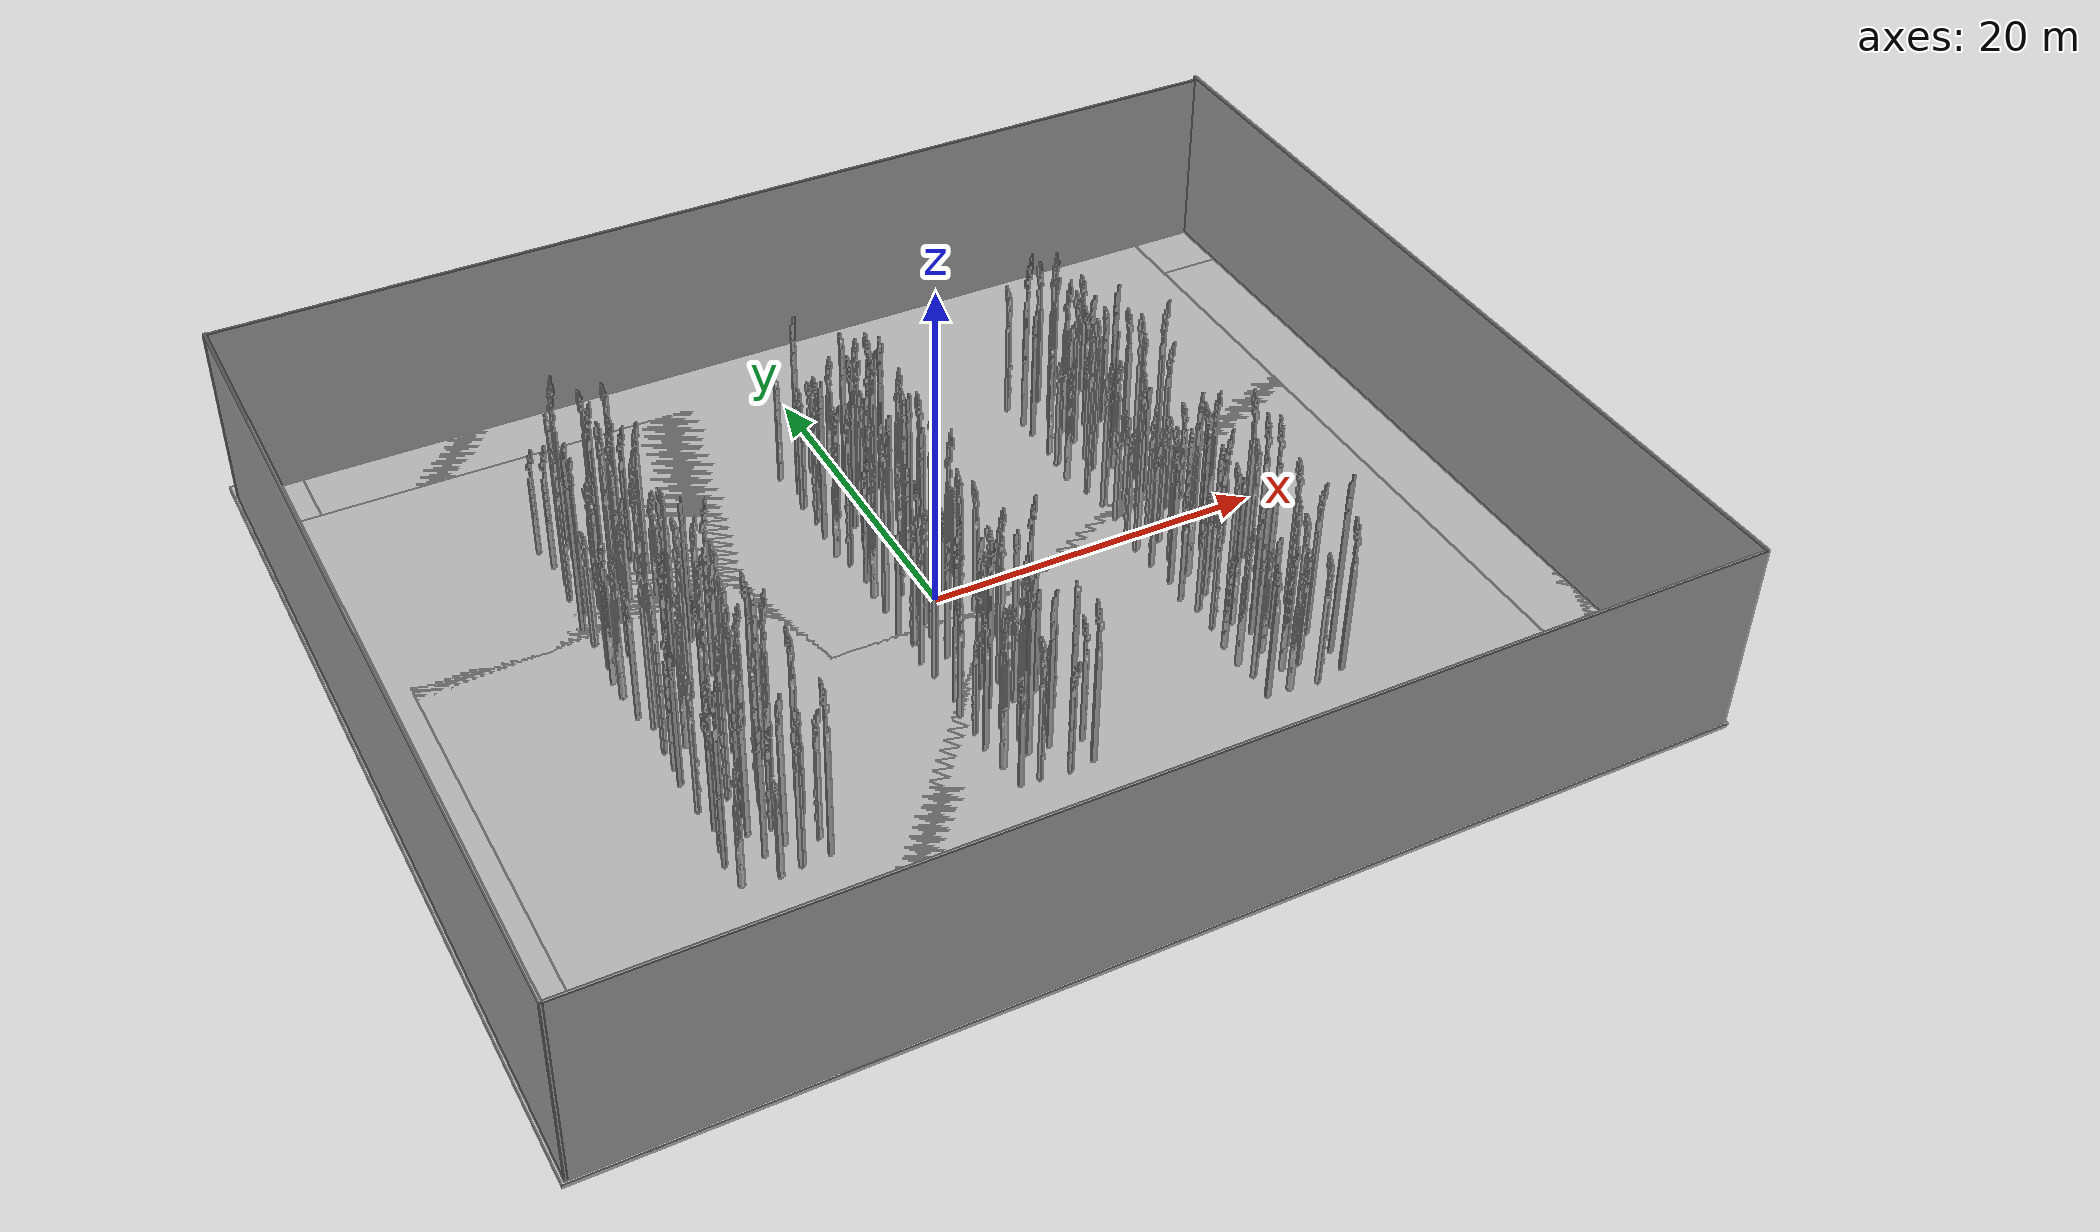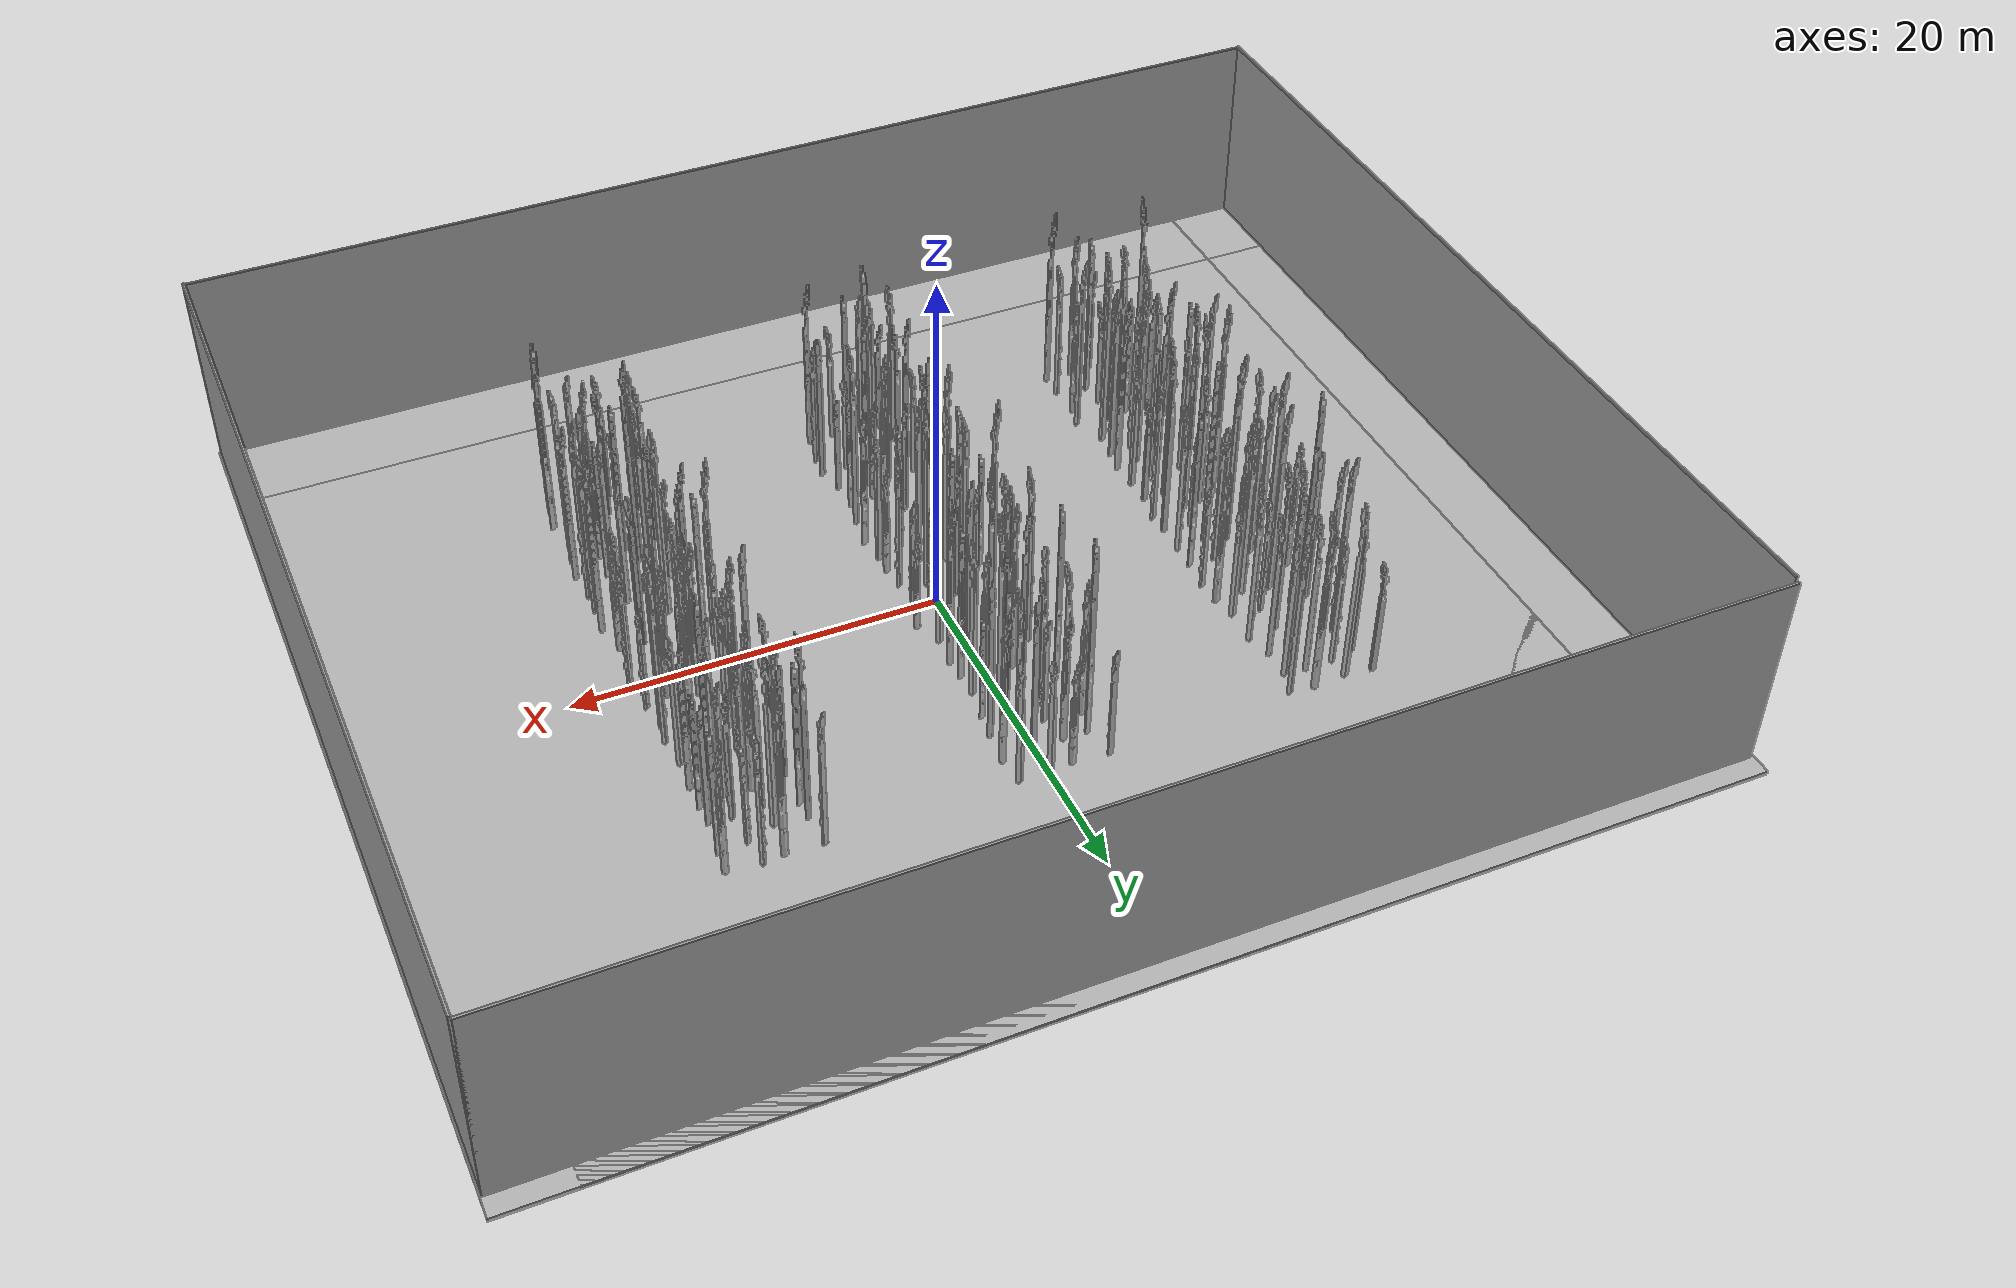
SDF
<sdf version="1.6">
 <world name="default">
  <atmosphere type="adiabatic"/>
  <wind><linear_velocity>0 0 0</linear_velocity></wind>
  <physics name="default_physics" default="1" type="ode">
   <max_step_size>0.001</max_step_size>
   <real_time_factor>1</real_time_factor>
   <real_time_update_rate>1000</real_time_update_rate>
  </physics>
  <gravity>0 0 -9.8</gravity>
  <model name="mud_box">
   <static>1</static>
   <link name="link">
    <collision name="collision"><geometry><box><size>120 100 2</size></box></geometry></collision>
    <visual name="visual_1">
     <pose>-2 2.5 0 0 -0 0</pose>
     <cast_shadows>0</cast_shadows>
     <geometry><box><size>60 50 0.2</size></box></geometry>
     <material>
      <script>
       <uri>model://mud_box/materials/scripts</uri>
       <uri>model://mud_box/materials/textures</uri>
       <name>vrc/mud</name>
      </script>
     </material>
    </visual>
    <visual name="visual_2">
     <pose>2 2.5 0 0 -0 0</pose>
     <cast_shadows>0</cast_shadows>
     <geometry><box><size>60 50 0.2</size></box></geometry>
     <material>
      <script>
       <uri>model://mud_box/materials/scripts</uri>
       <uri>model://mud_box/materials/textures</uri>
       <name>vrc/mud</name>
      </script>
     </material>
    </visual>
    <visual name="visual_3">
     <pose>2 -2.5 0 0 -0 0</pose>
     <cast_shadows>0</cast_shadows>
     <geometry><box><size>60 50 0.2</size></box></geometry>
     <material>
      <script>
       <uri>model://mud_box/materials/scripts</uri>
       <uri>model://mud_box/materials/textures</uri>
       <name>vrc/mud</name>
      </script>
     </material>
    </visual>
    <visual name="visual_4">
     <pose>-2 -2.5 0 0 -0 0</pose>
     <cast_shadows>0</cast_shadows>
     <geometry><box><size>60 50 0.2</size></box></geometry>
     <material>
      <script>
       <uri>model://mud_box/materials/scripts</uri>
       <uri>model://mud_box/materials/textures</uri>
       <name>vrc/mud</name>
      </script>
     </material>
    </visual>
   </link>
  </model>
  <light name="sun" type="directional">
   <pose>0 0 10 0 -0 0</pose>
   <diffuse>0.8 0.8 0.8 1</diffuse>
   <specular>0.2 0.2 0.2 1</specular>
   <attenuation>
    <range>1000</range>
    <constant>0.9</constant>
    <linear>0.01</linear>
    <quadratic>0.001</quadratic>
   </attenuation>
   <direction>-0.5 0.1 -0.9</direction>
  </light>
  <model name="asparagus_0">
   <pose>-18.0552 -14.9178 0 0 -0 0.13906</pose>
   <static>1</static>
   <link name="asparagus_0">
    <visual name="visual">
     <geometry>
      <mesh><uri>model://Asparagus/meshes/asparagus.obj</uri><scale>0.3 0.3 0.403627</scale></mesh>
     </geometry>
    </visual>
    <collision name="collision">
     <geometry>
      <mesh><uri>model://Asparagus/meshes/asparagus.obj</uri><scale>0.3 0.3 0.403627</scale></mesh>
     </geometry>
    </collision>
   </link>
  </model>
  <model name="asparagus_1">
   <pose>-2.90679 -14.8739 0 0 -0 2.77602</pose>
   <static>1</static>
   <link name="asparagus_1">
    <visual name="visual">
     <geometry>
      <mesh><uri>model://Asparagus/meshes/asparagus.obj</uri><scale>0.3 0.3 0.345911</scale></mesh>
     </geometry>
    </visual>
    <collision name="collision">
     <geometry>
      <mesh><uri>model://Asparagus/meshes/asparagus.obj</uri><scale>0.3 0.3 0.345911</scale></mesh>
     </geometry>
    </collision>
   </link>
  </model>
  <model name="asparagus_2">
   <pose>11.7751 -14.9194 0 0 -0 2.76325</pose>
   <static>1</static>
   <link name="asparagus_2">
    <visual name="visual">
     <geometry>
      <mesh><uri>model://Asparagus/meshes/asparagus.obj</uri><scale>0.3 0.3 0.43368</scale></mesh>
     </geometry>
    </visual>
    <collision name="collision">
     <geometry>
      <mesh><uri>model://Asparagus/meshes/asparagus.obj</uri><scale>0.3 0.3 0.43368</scale></mesh>
     </geometry>
    </collision>
   </link>
  </model>
  <model name="asparagus_3">
   <pose>-18.2997 -13.439 0 0 -0 -0.580635</pose>
   <static>1</static>
   <link name="asparagus_3">
    <visual name="visual">
     <geometry>
      <mesh><uri>model://Asparagus/meshes/asparagus.obj</uri><scale>0.3 0.3 0.595077</scale></mesh>
     </geometry>
    </visual>
    <collision name="collision">
     <geometry>
      <mesh><uri>model://Asparagus/meshes/asparagus.obj</uri><scale>0.3 0.3 0.595077</scale></mesh>
     </geometry>
    </collision>
   </link>
  </model>
  <model name="asparagus_4">
   <pose>-2.95804 -13.4201 0 0 -0 0.200583</pose>
   <static>1</static>
   <link name="asparagus_4">
    <visual name="visual">
     <geometry>
      <mesh><uri>model://Asparagus/meshes/asparagus.obj</uri><scale>0.3 0.3 0.517181</scale></mesh>
     </geometry>
    </visual>
    <collision name="collision">
     <geometry>
      <mesh><uri>model://Asparagus/meshes/asparagus.obj</uri><scale>0.3 0.3 0.517181</scale></mesh>
     </geometry>
    </collision>
   </link>
  </model>
  <model name="asparagus_5">
   <pose>11.9679 -13.3703 0 0 -0 -2.53466</pose>
   <static>1</static>
   <link name="asparagus_5">
    <visual name="visual">
     <geometry>
      <mesh><uri>model://Asparagus/meshes/asparagus.obj</uri><scale>0.3 0.3 0.44451</scale></mesh>
     </geometry>
    </visual>
    <collision name="collision">
     <geometry>
      <mesh><uri>model://Asparagus/meshes/asparagus.obj</uri><scale>0.3 0.3 0.44451</scale></mesh>
     </geometry>
    </collision>
   </link>
  </model>
  <model name="asparagus_6">
   <pose>-18.1559 -12.2868 0 0 -0 2.11804</pose>
   <static>1</static>
   <link name="asparagus_6">
    <visual name="visual">
     <geometry>
      <mesh><uri>model://Asparagus/meshes/asparagus.obj</uri><scale>0.3 0.3 0.370765</scale></mesh>
     </geometry>
    </visual>
    <collision name="collision">
     <geometry>
      <mesh><uri>model://Asparagus/meshes/asparagus.obj</uri><scale>0.3 0.3 0.370765</scale></mesh>
     </geometry>
    </collision>
   </link>
  </model>
  <model name="asparagus_7">
   <pose>-3.28311 -11.7764 0 0 -0 2.80035</pose>
   <static>1</static>
   <link name="asparagus_7">
    <visual name="visual">
     <geometry>
      <mesh><uri>model://Asparagus/meshes/asparagus.obj</uri><scale>0.3 0.3 0.457758</scale></mesh>
     </geometry>
    </visual>
    <collision name="collision">
     <geometry>
      <mesh><uri>model://Asparagus/meshes/asparagus.obj</uri><scale>0.3 0.3 0.457758</scale></mesh>
     </geometry>
    </collision>
   </link>
  </model>
  <model name="asparagus_8">
   <pose>11.8777 -12.1383 0 0 -0 -0.096665</pose>
   <static>1</static>
   <link name="asparagus_8">
    <visual name="visual">
     <geometry>
      <mesh><uri>model://Asparagus/meshes/asparagus.obj</uri><scale>0.3 0.3 0.444692</scale></mesh>
     </geometry>
    </visual>
    <collision name="collision">
     <geometry>
      <mesh><uri>model://Asparagus/meshes/asparagus.obj</uri><scale>0.3 0.3 0.444692</scale></mesh>
     </geometry>
    </collision>
   </link>
  </model>
  <model name="asparagus_9">
   <pose>-17.8685 -10.7495 0 0 -0 2.59011</pose>
   <static>1</static>
   <link name="asparagus_9">
    <visual name="visual">
     <geometry>
      <mesh><uri>model://Asparagus/meshes/asparagus.obj</uri><scale>0.3 0.3 0.375112</scale></mesh>
     </geometry>
    </visual>
    <collision name="collision">
     <geometry>
      <mesh><uri>model://Asparagus/meshes/asparagus.obj</uri><scale>0.3 0.3 0.375112</scale></mesh>
     </geometry>
    </collision>
   </link>
  </model>
  <model name="asparagus_10">
   <pose>-3.06272 -10.5367 0 0 -0 -1.03703</pose>
   <static>1</static>
   <link name="asparagus_10">
    <visual name="visual">
     <geometry>
      <mesh><uri>model://Asparagus/meshes/asparagus.obj</uri><scale>0.3 0.3 0.337028</scale></mesh>
     </geometry>
    </visual>
    <collision name="collision">
     <geometry>
      <mesh><uri>model://Asparagus/meshes/asparagus.obj</uri><scale>0.3 0.3 0.337028</scale></mesh>
     </geometry>
    </collision>
   </link>
  </model>
  <model name="asparagus_11">
   <pose>11.9933 -10.5922 0 0 -0 -0.335565</pose>
   <static>1</static>
   <link name="asparagus_11">
    <visual name="visual">
     <geometry>
      <mesh><uri>model://Asparagus/meshes/asparagus.obj</uri><scale>0.3 0.3 0.313973</scale></mesh>
     </geometry>
    </visual>
    <collision name="collision">
     <geometry>
      <mesh><uri>model://Asparagus/meshes/asparagus.obj</uri><scale>0.3 0.3 0.313973</scale></mesh>
     </geometry>
    </collision>
   </link>
  </model>
  <model name="asparagus_12">
   <pose>-18.0938 -9.28618 0 0 -0 1.98206</pose>
   <static>1</static>
   <link name="asparagus_12">
    <visual name="visual">
     <geometry>
      <mesh><uri>model://Asparagus/meshes/asparagus.obj</uri><scale>0.3 0.3 0.453931</scale></mesh>
     </geometry>
    </visual>
    <collision name="collision">
     <geometry>
      <mesh><uri>model://Asparagus/meshes/asparagus.obj</uri><scale>0.3 0.3 0.453931</scale></mesh>
     </geometry>
    </collision>
   </link>
  </model>
  <model name="asparagus_13">
   <pose>-3.26129 -8.95838 0 0 -0 2.18305</pose>
   <static>1</static>
   <link name="asparagus_13">
    <visual name="visual">
     <geometry>
      <mesh><uri>model://Asparagus/meshes/asparagus.obj</uri><scale>0.3 0.3 0.392294</scale></mesh>
     </geometry>
    </visual>
    <collision name="collision">
     <geometry>
      <mesh><uri>model://Asparagus/meshes/asparagus.obj</uri><scale>0.3 0.3 0.392294</scale></mesh>
     </geometry>
    </collision>
   </link>
  </model>
  <model name="asparagus_14">
   <pose>12.1264 -8.9274 0 0 -0 1.63535</pose>
   <static>1</static>
   <link name="asparagus_14">
    <visual name="visual">
     <geometry>
      <mesh><uri>model://Asparagus/meshes/asparagus.obj</uri><scale>0.3 0.3 0.379227</scale></mesh>
     </geometry>
    </visual>
    <collision name="collision">
     <geometry>
      <mesh><uri>model://Asparagus/meshes/asparagus.obj</uri><scale>0.3 0.3 0.379227</scale></mesh>
     </geometry>
    </collision>
   </link>
  </model>
  <model name="asparagus_15">
   <pose>-18.1342 -7.25989 0 0 -0 -2.06988</pose>
   <static>1</static>
   <link name="asparagus_15">
    <visual name="visual">
     <geometry>
      <mesh><uri>model://Asparagus/meshes/asparagus.obj</uri><scale>0.3 0.3 0.440702</scale></mesh>
     </geometry>
    </visual>
    <collision name="collision">
     <geometry>
      <mesh><uri>model://Asparagus/meshes/asparagus.obj</uri><scale>0.3 0.3 0.440702</scale></mesh>
     </geometry>
    </collision>
   </link>
  </model>
  <model name="asparagus_16">
   <pose>-2.85009 -7.74077 0 0 -0 1.05702</pose>
   <static>1</static>
   <link name="asparagus_16">
    <visual name="visual">
     <geometry>
      <mesh><uri>model://Asparagus/meshes/asparagus.obj</uri><scale>0.3 0.3 0.474499</scale></mesh>
     </geometry>
    </visual>
    <collision name="collision">
     <geometry>
      <mesh><uri>model://Asparagus/meshes/asparagus.obj</uri><scale>0.3 0.3 0.474499</scale></mesh>
     </geometry>
    </collision>
   </link>
  </model>
  <model name="asparagus_17">
   <pose>12.2011 -7.40612 0 0 -0 -2.67844</pose>
   <static>1</static>
   <link name="asparagus_17">
    <visual name="visual">
     <geometry>
      <mesh><uri>model://Asparagus/meshes/asparagus.obj</uri><scale>0.3 0.3 0.309955</scale></mesh>
     </geometry>
    </visual>
    <collision name="collision">
     <geometry>
      <mesh><uri>model://Asparagus/meshes/asparagus.obj</uri><scale>0.3 0.3 0.309955</scale></mesh>
     </geometry>
    </collision>
   </link>
  </model>
  <model name="asparagus_18">
   <pose>-17.8814 -6.02138 0 0 -0 -0.277155</pose>
   <static>1</static>
   <link name="asparagus_18">
    <visual name="visual">
     <geometry>
      <mesh><uri>model://Asparagus/meshes/asparagus.obj</uri><scale>0.3 0.3 0.48757</scale></mesh>
     </geometry>
    </visual>
    <collision name="collision">
     <geometry>
      <mesh><uri>model://Asparagus/meshes/asparagus.obj</uri><scale>0.3 0.3 0.48757</scale></mesh>
     </geometry>
    </collision>
   </link>
  </model>
  <model name="asparagus_19">
   <pose>-3.07164 -5.75902 0 0 -0 -2.6461</pose>
   <static>1</static>
   <link name="asparagus_19">
    <visual name="visual">
     <geometry>
      <mesh><uri>model://Asparagus/meshes/asparagus.obj</uri><scale>0.3 0.3 0.500914</scale></mesh>
     </geometry>
    </visual>
    <collision name="collision">
     <geometry>
      <mesh><uri>model://Asparagus/meshes/asparagus.obj</uri><scale>0.3 0.3 0.500914</scale></mesh>
     </geometry>
    </collision>
   </link>
  </model>
  <model name="asparagus_20">
   <pose>11.8231 -6.08831 0 0 -0 2.40759</pose>
   <static>1</static>
   <link name="asparagus_20">
    <visual name="visual">
     <geometry>
      <mesh><uri>model://Asparagus/meshes/asparagus.obj</uri><scale>0.3 0.3 0.347144</scale></mesh>
     </geometry>
    </visual>
    <collision name="collision">
     <geometry>
      <mesh><uri>model://Asparagus/meshes/asparagus.obj</uri><scale>0.3 0.3 0.347144</scale></mesh>
     </geometry>
    </collision>
   </link>
  </model>
  <model name="asparagus_21">
   <pose>-17.9789 -4.61451 0 0 -0 1.82332</pose>
   <static>1</static>
   <link name="asparagus_21">
    <visual name="visual">
     <geometry>
      <mesh><uri>model://Asparagus/meshes/asparagus.obj</uri><scale>0.3 0.3 0.558133</scale></mesh>
     </geometry>
    </visual>
    <collision name="collision">
     <geometry>
      <mesh><uri>model://Asparagus/meshes/asparagus.obj</uri><scale>0.3 0.3 0.558133</scale></mesh>
     </geometry>
    </collision>
   </link>
  </model>
  <model name="asparagus_22">
   <pose>-3.15192 -4.45805 0 0 -0 -1.46436</pose>
   <static>1</static>
   <link name="asparagus_22">
    <visual name="visual">
     <geometry>
      <mesh><uri>model://Asparagus/meshes/asparagus.obj</uri><scale>0.3 0.3 0.415043</scale></mesh>
     </geometry>
    </visual>
    <collision name="collision">
     <geometry>
      <mesh><uri>model://Asparagus/meshes/asparagus.obj</uri><scale>0.3 0.3 0.415043</scale></mesh>
     </geometry>
    </collision>
   </link>
  </model>
  <model name="asparagus_23">
   <pose>12.0275 -4.61338 0 0 -0 2.80308</pose>
   <static>1</static>
   <link name="asparagus_23">
    <visual name="visual">
     <geometry>
      <mesh><uri>model://Asparagus/meshes/asparagus.obj</uri><scale>0.3 0.3 0.466317</scale></mesh>
     </geometry>
    </visual>
    <collision name="collision">
     <geometry>
      <mesh><uri>model://Asparagus/meshes/asparagus.obj</uri><scale>0.3 0.3 0.466317</scale></mesh>
     </geometry>
    </collision>
   </link>
  </model>
  <model name="asparagus_24">
   <pose>-17.7862 -2.78715 0 0 -0 -2.65873</pose>
   <static>1</static>
   <link name="asparagus_24">
    <visual name="visual">
     <geometry>
      <mesh><uri>model://Asparagus/meshes/asparagus.obj</uri><scale>0.3 0.3 0.575133</scale></mesh>
     </geometry>
    </visual>
    <collision name="collision">
     <geometry>
      <mesh><uri>model://Asparagus/meshes/asparagus.obj</uri><scale>0.3 0.3 0.575133</scale></mesh>
     </geometry>
    </collision>
   </link>
  </model>
  <model name="asparagus_25">
   <pose>-2.8218 -2.93972 0 0 -0 -1.17502</pose>
   <static>1</static>
   <link name="asparagus_25">
    <visual name="visual">
     <geometry>
      <mesh><uri>model://Asparagus/meshes/asparagus.obj</uri><scale>0.3 0.3 0.434295</scale></mesh>
     </geometry>
    </visual>
    <collision name="collision">
     <geometry>
      <mesh><uri>model://Asparagus/meshes/asparagus.obj</uri><scale>0.3 0.3 0.434295</scale></mesh>
     </geometry>
    </collision>
   </link>
  </model>
  <model name="asparagus_26">
   <pose>11.9356 -2.94938 0 0 -0 -1.71101</pose>
   <static>1</static>
   <link name="asparagus_26">
    <visual name="visual">
     <geometry>
      <mesh><uri>model://Asparagus/meshes/asparagus.obj</uri><scale>0.3 0.3 0.423964</scale></mesh>
     </geometry>
    </visual>
    <collision name="collision">
     <geometry>
      <mesh><uri>model://Asparagus/meshes/asparagus.obj</uri><scale>0.3 0.3 0.423964</scale></mesh>
     </geometry>
    </collision>
   </link>
  </model>
  <model name="asparagus_27">
   <pose>-18.2786 -1.60323 0 0 -0 2.78824</pose>
   <static>1</static>
   <link name="asparagus_27">
    <visual name="visual">
     <geometry>
      <mesh><uri>model://Asparagus/meshes/asparagus.obj</uri><scale>0.3 0.3 0.458468</scale></mesh>
     </geometry>
    </visual>
    <collision name="collision">
     <geometry>
      <mesh><uri>model://Asparagus/meshes/asparagus.obj</uri><scale>0.3 0.3 0.458468</scale></mesh>
     </geometry>
    </collision>
   </link>
  </model>
  <model name="asparagus_28">
   <pose>-3.18675 -1.78446 0 0 -0 -1.98127</pose>
   <static>1</static>
   <link name="asparagus_28">
    <visual name="visual">
     <geometry>
      <mesh><uri>model://Asparagus/meshes/asparagus.obj</uri><scale>0.3 0.3 0.353589</scale></mesh>
     </geometry>
    </visual>
    <collision name="collision">
     <geometry>
      <mesh><uri>model://Asparagus/meshes/asparagus.obj</uri><scale>0.3 0.3 0.353589</scale></mesh>
     </geometry>
    </collision>
   </link>
  </model>
  <model name="asparagus_29">
   <pose>11.7423 -1.42219 0 0 -0 -3.09264</pose>
   <static>1</static>
   <link name="asparagus_29">
    <visual name="visual">
     <geometry>
      <mesh><uri>model://Asparagus/meshes/asparagus.obj</uri><scale>0.3 0.3 0.582399</scale></mesh>
     </geometry>
    </visual>
    <collision name="collision">
     <geometry>
      <mesh><uri>model://Asparagus/meshes/asparagus.obj</uri><scale>0.3 0.3 0.582399</scale></mesh>
     </geometry>
    </collision>
   </link>
  </model>
  <model name="asparagus_30">
   <pose>-18.2426 0.221658 0 0 -0 0.227744</pose>
   <static>1</static>
   <link name="asparagus_30">
    <visual name="visual">
     <geometry>
      <mesh><uri>model://Asparagus/meshes/asparagus.obj</uri><scale>0.3 0.3 0.477221</scale></mesh>
     </geometry>
    </visual>
    <collision name="collision">
     <geometry>
      <mesh><uri>model://Asparagus/meshes/asparagus.obj</uri><scale>0.3 0.3 0.477221</scale></mesh>
     </geometry>
    </collision>
   </link>
  </model>
  <model name="asparagus_31">
   <pose>-3.09188 0.178459 0 0 -0 -3.05527</pose>
   <static>1</static>
   <link name="asparagus_31">
    <visual name="visual">
     <geometry>
      <mesh><uri>model://Asparagus/meshes/asparagus.obj</uri><scale>0.3 0.3 0.589458</scale></mesh>
     </geometry>
    </visual>
    <collision name="collision">
     <geometry>
      <mesh><uri>model://Asparagus/meshes/asparagus.obj</uri><scale>0.3 0.3 0.589458</scale></mesh>
     </geometry>
    </collision>
   </link>
  </model>
  <model name="asparagus_32">
   <pose>12.2089 0.181974 0 0 -0 -1.14606</pose>
   <static>1</static>
   <link name="asparagus_32">
    <visual name="visual">
     <geometry>
      <mesh><uri>model://Asparagus/meshes/asparagus.obj</uri><scale>0.3 0.3 0.359142</scale></mesh>
     </geometry>
    </visual>
    <collision name="collision">
     <geometry>
      <mesh><uri>model://Asparagus/meshes/asparagus.obj</uri><scale>0.3 0.3 0.359142</scale></mesh>
     </geometry>
    </collision>
   </link>
  </model>
  <model name="asparagus_33">
   <pose>-18.2865 1.57433 0 0 -0 0.87551</pose>
   <static>1</static>
   <link name="asparagus_33">
    <visual name="visual">
     <geometry>
      <mesh><uri>model://Asparagus/meshes/asparagus.obj</uri><scale>0.3 0.3 0.469335</scale></mesh>
     </geometry>
    </visual>
    <collision name="collision">
     <geometry>
      <mesh><uri>model://Asparagus/meshes/asparagus.obj</uri><scale>0.3 0.3 0.469335</scale></mesh>
     </geometry>
    </collision>
   </link>
  </model>
  <model name="asparagus_34">
   <pose>-2.93227 1.688 0 0 -0 0.311129</pose>
   <static>1</static>
   <link name="asparagus_34">
    <visual name="visual">
     <geometry>
      <mesh><uri>model://Asparagus/meshes/asparagus.obj</uri><scale>0.3 0.3 0.430906</scale></mesh>
     </geometry>
    </visual>
    <collision name="collision">
     <geometry>
      <mesh><uri>model://Asparagus/meshes/asparagus.obj</uri><scale>0.3 0.3 0.430906</scale></mesh>
     </geometry>
    </collision>
   </link>
  </model>
  <model name="asparagus_35">
   <pose>12.2317 1.62877 0 0 -0 -2.67471</pose>
   <static>1</static>
   <link name="asparagus_35">
    <visual name="visual">
     <geometry>
      <mesh><uri>model://Asparagus/meshes/asparagus.obj</uri><scale>0.3 0.3 0.303656</scale></mesh>
     </geometry>
    </visual>
    <collision name="collision">
     <geometry>
      <mesh><uri>model://Asparagus/meshes/asparagus.obj</uri><scale>0.3 0.3 0.303656</scale></mesh>
     </geometry>
    </collision>
   </link>
  </model>
  <model name="asparagus_36">
   <pose>-18.1309 2.79364 0 0 -0 1.51272</pose>
   <static>1</static>
   <link name="asparagus_36">
    <visual name="visual">
     <geometry>
      <mesh><uri>model://Asparagus/meshes/asparagus.obj</uri><scale>0.3 0.3 0.551831</scale></mesh>
     </geometry>
    </visual>
    <collision name="collision">
     <geometry>
      <mesh><uri>model://Asparagus/meshes/asparagus.obj</uri><scale>0.3 0.3 0.551831</scale></mesh>
     </geometry>
    </collision>
   </link>
  </model>
  <model name="asparagus_37">
   <pose>-2.73111 3.00816 0 0 -0 -0.526085</pose>
   <static>1</static>
   <link name="asparagus_37">
    <visual name="visual">
     <geometry>
      <mesh><uri>model://Asparagus/meshes/asparagus.obj</uri><scale>0.3 0.3 0.429202</scale></mesh>
     </geometry>
    </visual>
    <collision name="collision">
     <geometry>
      <mesh><uri>model://Asparagus/meshes/asparagus.obj</uri><scale>0.3 0.3 0.429202</scale></mesh>
     </geometry>
    </collision>
   </link>
  </model>
  <model name="asparagus_38">
   <pose>12.1933 2.97313 0 0 -0 -2.66477</pose>
   <static>1</static>
   <link name="asparagus_38">
    <visual name="visual">
     <geometry>
      <mesh><uri>model://Asparagus/meshes/asparagus.obj</uri><scale>0.3 0.3 0.452807</scale></mesh>
     </geometry>
    </visual>
    <collision name="collision">
     <geometry>
      <mesh><uri>model://Asparagus/meshes/asparagus.obj</uri><scale>0.3 0.3 0.452807</scale></mesh>
     </geometry>
    </collision>
   </link>
  </model>
  <model name="asparagus_39">
   <pose>-18.1932 4.73271 0 0 -0 -2.64593</pose>
   <static>1</static>
   <link name="asparagus_39">
    <visual name="visual">
     <geometry>
      <mesh><uri>model://Asparagus/meshes/asparagus.obj</uri><scale>0.3 0.3 0.389807</scale></mesh>
     </geometry>
    </visual>
    <collision name="collision">
     <geometry>
      <mesh><uri>model://Asparagus/meshes/asparagus.obj</uri><scale>0.3 0.3 0.389807</scale></mesh>
     </geometry>
    </collision>
   </link>
  </model>
  <model name="asparagus_40">
   <pose>-2.95805 4.64346 0 0 -0 -0.885135</pose>
   <static>1</static>
   <link name="asparagus_40">
    <visual name="visual">
     <geometry>
      <mesh><uri>model://Asparagus/meshes/asparagus.obj</uri><scale>0.3 0.3 0.549346</scale></mesh>
     </geometry>
    </visual>
    <collision name="collision">
     <geometry>
      <mesh><uri>model://Asparagus/meshes/asparagus.obj</uri><scale>0.3 0.3 0.549346</scale></mesh>
     </geometry>
    </collision>
   </link>
  </model>
  <model name="asparagus_41">
   <pose>11.9973 4.55182 0 0 -0 1.61893</pose>
   <static>1</static>
   <link name="asparagus_41">
    <visual name="visual">
     <geometry>
      <mesh><uri>model://Asparagus/meshes/asparagus.obj</uri><scale>0.3 0.3 0.556947</scale></mesh>
     </geometry>
    </visual>
    <collision name="collision">
     <geometry>
      <mesh><uri>model://Asparagus/meshes/asparagus.obj</uri><scale>0.3 0.3 0.556947</scale></mesh>
     </geometry>
    </collision>
   </link>
  </model>
  <model name="asparagus_42">
   <pose>-18.2793 6.12615 0 0 -0 -1.99663</pose>
   <static>1</static>
   <link name="asparagus_42">
    <visual name="visual">
     <geometry>
      <mesh><uri>model://Asparagus/meshes/asparagus.obj</uri><scale>0.3 0.3 0.590509</scale></mesh>
     </geometry>
    </visual>
    <collision name="collision">
     <geometry>
      <mesh><uri>model://Asparagus/meshes/asparagus.obj</uri><scale>0.3 0.3 0.590509</scale></mesh>
     </geometry>
    </collision>
   </link>
  </model>
  <model name="asparagus_43">
   <pose>-3.2419 5.9099 0 0 -0 0.706755</pose>
   <static>1</static>
   <link name="asparagus_43">
    <visual name="visual">
     <geometry>
      <mesh><uri>model://Asparagus/meshes/asparagus.obj</uri><scale>0.3 0.3 0.356486</scale></mesh>
     </geometry>
    </visual>
    <collision name="collision">
     <geometry>
      <mesh><uri>model://Asparagus/meshes/asparagus.obj</uri><scale>0.3 0.3 0.356486</scale></mesh>
     </geometry>
    </collision>
   </link>
  </model>
  <model name="asparagus_44">
   <pose>11.7162 6.16978 0 0 -0 -0.231285</pose>
   <static>1</static>
   <link name="asparagus_44">
    <visual name="visual">
     <geometry>
      <mesh><uri>model://Asparagus/meshes/asparagus.obj</uri><scale>0.3 0.3 0.405773</scale></mesh>
     </geometry>
    </visual>
    <collision name="collision">
     <geometry>
      <mesh><uri>model://Asparagus/meshes/asparagus.obj</uri><scale>0.3 0.3 0.405773</scale></mesh>
     </geometry>
    </collision>
   </link>
  </model>
  <model name="asparagus_45">
   <pose>-17.7572 7.4547 0 0 -0 0.73391</pose>
   <static>1</static>
   <link name="asparagus_45">
    <visual name="visual">
     <geometry>
      <mesh><uri>model://Asparagus/meshes/asparagus.obj</uri><scale>0.3 0.3 0.474122</scale></mesh>
     </geometry>
    </visual>
    <collision name="collision">
     <geometry>
      <mesh><uri>model://Asparagus/meshes/asparagus.obj</uri><scale>0.3 0.3 0.474122</scale></mesh>
     </geometry>
    </collision>
   </link>
  </model>
  <model name="asparagus_46">
   <pose>-3.25257 7.49353 0 0 -0 -1.967</pose>
   <static>1</static>
   <link name="asparagus_46">
    <visual name="visual">
     <geometry>
      <mesh><uri>model://Asparagus/meshes/asparagus.obj</uri><scale>0.3 0.3 0.529041</scale></mesh>
     </geometry>
    </visual>
    <collision name="collision">
     <geometry>
      <mesh><uri>model://Asparagus/meshes/asparagus.obj</uri><scale>0.3 0.3 0.529041</scale></mesh>
     </geometry>
    </collision>
   </link>
  </model>
  <model name="asparagus_47">
   <pose>11.7378 7.58479 0 0 -0 -2.63692</pose>
   <static>1</static>
   <link name="asparagus_47">
    <visual name="visual">
     <geometry>
      <mesh><uri>model://Asparagus/meshes/asparagus.obj</uri><scale>0.3 0.3 0.360139</scale></mesh>
     </geometry>
    </visual>
    <collision name="collision">
     <geometry>
      <mesh><uri>model://Asparagus/meshes/asparagus.obj</uri><scale>0.3 0.3 0.360139</scale></mesh>
     </geometry>
    </collision>
   </link>
  </model>
  <model name="asparagus_48">
   <pose>-18.0313 8.99182 0 0 -0 1.87498</pose>
   <static>1</static>
   <link name="asparagus_48">
    <visual name="visual">
     <geometry>
      <mesh><uri>model://Asparagus/meshes/asparagus.obj</uri><scale>0.3 0.3 0.49781</scale></mesh>
     </geometry>
    </visual>
    <collision name="collision">
     <geometry>
      <mesh><uri>model://Asparagus/meshes/asparagus.obj</uri><scale>0.3 0.3 0.49781</scale></mesh>
     </geometry>
    </collision>
   </link>
  </model>
  <model name="asparagus_49">
   <pose>-3.01257 8.94992 0 0 -0 -0.954125</pose>
   <static>1</static>
   <link name="asparagus_49">
    <visual name="visual">
     <geometry>
      <mesh><uri>model://Asparagus/meshes/asparagus.obj</uri><scale>0.3 0.3 0.417573</scale></mesh>
     </geometry>
    </visual>
    <collision name="collision">
     <geometry>
      <mesh><uri>model://Asparagus/meshes/asparagus.obj</uri><scale>0.3 0.3 0.417573</scale></mesh>
     </geometry>
    </collision>
   </link>
  </model>
  <model name="asparagus_50">
   <pose>11.9252 8.88474 0 0 -0 1.19123</pose>
   <static>1</static>
   <link name="asparagus_50">
    <visual name="visual">
     <geometry>
      <mesh><uri>model://Asparagus/meshes/asparagus.obj</uri><scale>0.3 0.3 0.366326</scale></mesh>
     </geometry>
    </visual>
    <collision name="collision">
     <geometry>
      <mesh><uri>model://Asparagus/meshes/asparagus.obj</uri><scale>0.3 0.3 0.366326</scale></mesh>
     </geometry>
    </collision>
   </link>
  </model>
  <model name="asparagus_51">
   <pose>-17.7103 10.3318 0 0 -0 1.56315</pose>
   <static>1</static>
   <link name="asparagus_51">
    <visual name="visual">
     <geometry>
      <mesh><uri>model://Asparagus/meshes/asparagus.obj</uri><scale>0.3 0.3 0.556655</scale></mesh>
     </geometry>
    </visual>
    <collision name="collision">
     <geometry>
      <mesh><uri>model://Asparagus/meshes/asparagus.obj</uri><scale>0.3 0.3 0.556655</scale></mesh>
     </geometry>
    </collision>
   </link>
  </model>
  <model name="asparagus_52">
   <pose>-3.22845 10.5608 0 0 -0 -2.63449</pose>
   <static>1</static>
   <link name="asparagus_52">
    <visual name="visual">
     <geometry>
      <mesh><uri>model://Asparagus/meshes/asparagus.obj</uri><scale>0.3 0.3 0.416963</scale></mesh>
     </geometry>
    </visual>
    <collision name="collision">
     <geometry>
      <mesh><uri>model://Asparagus/meshes/asparagus.obj</uri><scale>0.3 0.3 0.416963</scale></mesh>
     </geometry>
    </collision>
   </link>
  </model>
  <model name="asparagus_53">
   <pose>11.8709 10.7469 0 0 -0 -2.00169</pose>
   <static>1</static>
   <link name="asparagus_53">
    <visual name="visual">
     <geometry>
      <mesh><uri>model://Asparagus/meshes/asparagus.obj</uri><scale>0.3 0.3 0.435216</scale></mesh>
     </geometry>
    </visual>
    <collision name="collision">
     <geometry>
      <mesh><uri>model://Asparagus/meshes/asparagus.obj</uri><scale>0.3 0.3 0.435216</scale></mesh>
     </geometry>
    </collision>
   </link>
  </model>
  <model name="asparagus_54">
   <pose>-17.7062 11.9879 0 0 -0 -0.200105</pose>
   <static>1</static>
   <link name="asparagus_54">
    <visual name="visual">
     <geometry>
      <mesh><uri>model://Asparagus/meshes/asparagus.obj</uri><scale>0.3 0.3 0.412093</scale></mesh>
     </geometry>
    </visual>
    <collision name="collision">
     <geometry>
      <mesh><uri>model://Asparagus/meshes/asparagus.obj</uri><scale>0.3 0.3 0.412093</scale></mesh>
     </geometry>
    </collision>
   </link>
  </model>
  <model name="asparagus_55">
   <pose>-2.83045 11.9065 0 0 -0 -1.87174</pose>
   <static>1</static>
   <link name="asparagus_55">
    <visual name="visual">
     <geometry>
      <mesh><uri>model://Asparagus/meshes/asparagus.obj</uri><scale>0.3 0.3 0.596701</scale></mesh>
     </geometry>
    </visual>
    <collision name="collision">
     <geometry>
      <mesh><uri>model://Asparagus/meshes/asparagus.obj</uri><scale>0.3 0.3 0.596701</scale></mesh>
     </geometry>
    </collision>
   </link>
  </model>
  <model name="asparagus_56">
   <pose>11.9555 11.8867 0 0 -0 -0.396675</pose>
   <static>1</static>
   <link name="asparagus_56">
    <visual name="visual">
     <geometry>
      <mesh><uri>model://Asparagus/meshes/asparagus.obj</uri><scale>0.3 0.3 0.581473</scale></mesh>
     </geometry>
    </visual>
    <collision name="collision">
     <geometry>
      <mesh><uri>model://Asparagus/meshes/asparagus.obj</uri><scale>0.3 0.3 0.581473</scale></mesh>
     </geometry>
    </collision>
   </link>
  </model>
  <model name="asparagus_57">
   <pose>-18.0025 13.6079 0 0 -0 -0.248765</pose>
   <static>1</static>
   <link name="asparagus_57">
    <visual name="visual">
     <geometry>
      <mesh><uri>model://Asparagus/meshes/asparagus.obj</uri><scale>0.3 0.3 0.352447</scale></mesh>
     </geometry>
    </visual>
    <collision name="collision">
     <geometry>
      <mesh><uri>model://Asparagus/meshes/asparagus.obj</uri><scale>0.3 0.3 0.352447</scale></mesh>
     </geometry>
    </collision>
   </link>
  </model>
  <model name="asparagus_58">
   <pose>-3.23287 13.7624 0 0 -0 1.40347</pose>
   <static>1</static>
   <link name="asparagus_58">
    <visual name="visual">
     <geometry>
      <mesh><uri>model://Asparagus/meshes/asparagus.obj</uri><scale>0.3 0.3 0.341846</scale></mesh>
     </geometry>
    </visual>
    <collision name="collision">
     <geometry>
      <mesh><uri>model://Asparagus/meshes/asparagus.obj</uri><scale>0.3 0.3 0.341846</scale></mesh>
     </geometry>
    </collision>
   </link>
  </model>
  <model name="asparagus_59">
   <pose>11.7198 13.7906 0 0 -0 1.77032</pose>
   <static>1</static>
   <link name="asparagus_59">
    <visual name="visual">
     <geometry>
      <mesh><uri>model://Asparagus/meshes/asparagus.obj</uri><scale>0.3 0.3 0.425991</scale></mesh>
     </geometry>
    </visual>
    <collision name="collision">
     <geometry>
      <mesh><uri>model://Asparagus/meshes/asparagus.obj</uri><scale>0.3 0.3 0.425991</scale></mesh>
     </geometry>
    </collision>
   </link>
  </model>
  <model name="asparagus_60">
   <pose>-16.2742 -15.2325 0 0 -0 3.12725</pose>
   <static>1</static>
   <link name="asparagus_60">
    <visual name="visual">
     <geometry>
      <mesh><uri>model://Asparagus/meshes/asparagus.obj</uri><scale>0.3 0.3 0.32586</scale></mesh>
     </geometry>
    </visual>
    <collision name="collision">
     <geometry>
      <mesh><uri>model://Asparagus/meshes/asparagus.obj</uri><scale>0.3 0.3 0.32586</scale></mesh>
     </geometry>
    </collision>
   </link>
  </model>
  <model name="asparagus_61">
   <pose>-1.78048 -14.9473 0 0 -0 1.76297</pose>
   <static>1</static>
   <link name="asparagus_61">
    <visual name="visual">
     <geometry>
      <mesh><uri>model://Asparagus/meshes/asparagus.obj</uri><scale>0.3 0.3 0.4556</scale></mesh>
     </geometry>
    </visual>
    <collision name="collision">
     <geometry>
      <mesh><uri>model://Asparagus/meshes/asparagus.obj</uri><scale>0.3 0.3 0.4556</scale></mesh>
     </geometry>
    </collision>
   </link>
  </model>
  <model name="asparagus_62">
   <pose>13.261 -15.0041 0 0 -0 -0.025895</pose>
   <static>1</static>
   <link name="asparagus_62">
    <visual name="visual">
     <geometry>
      <mesh><uri>model://Asparagus/meshes/asparagus.obj</uri><scale>0.3 0.3 0.404513</scale></mesh>
     </geometry>
    </visual>
    <collision name="collision">
     <geometry>
      <mesh><uri>model://Asparagus/meshes/asparagus.obj</uri><scale>0.3 0.3 0.404513</scale></mesh>
     </geometry>
    </collision>
   </link>
  </model>
  <model name="asparagus_63">
   <pose>-16.3407 -13.704 0 0 -0 -1.90725</pose>
   <static>1</static>
   <link name="asparagus_63">
    <visual name="visual">
     <geometry>
      <mesh><uri>model://Asparagus/meshes/asparagus.obj</uri><scale>0.3 0.3 0.430193</scale></mesh>
     </geometry>
    </visual>
    <collision name="collision">
     <geometry>
      <mesh><uri>model://Asparagus/meshes/asparagus.obj</uri><scale>0.3 0.3 0.430193</scale></mesh>
     </geometry>
    </collision>
   </link>
  </model>
  <model name="asparagus_64">
   <pose>-1.41383 -13.2106 0 0 -0 -1.61654</pose>
   <static>1</static>
   <link name="asparagus_64">
    <visual name="visual">
     <geometry>
      <mesh><uri>model://Asparagus/meshes/asparagus.obj</uri><scale>0.3 0.3 0.595208</scale></mesh>
     </geometry>
    </visual>
    <collision name="collision">
     <geometry>
      <mesh><uri>model://Asparagus/meshes/asparagus.obj</uri><scale>0.3 0.3 0.595208</scale></mesh>
     </geometry>
    </collision>
   </link>
  </model>
  <model name="asparagus_65">
   <pose>13.7354 -13.5335 0 0 -0 -0.341545</pose>
   <static>1</static>
   <link name="asparagus_65">
    <visual name="visual">
     <geometry>
      <mesh><uri>model://Asparagus/meshes/asparagus.obj</uri><scale>0.3 0.3 0.401042</scale></mesh>
     </geometry>
    </visual>
    <collision name="collision">
     <geometry>
      <mesh><uri>model://Asparagus/meshes/asparagus.obj</uri><scale>0.3 0.3 0.401042</scale></mesh>
     </geometry>
    </collision>
   </link>
  </model>
  <model name="asparagus_66">
   <pose>-16.5134 -12.005 0 0 -0 -1.66874</pose>
   <static>1</static>
   <link name="asparagus_66">
    <visual name="visual">
     <geometry>
      <mesh><uri>model://Asparagus/meshes/asparagus.obj</uri><scale>0.3 0.3 0.435638</scale></mesh>
     </geometry>
    </visual>
    <collision name="collision">
     <geometry>
      <mesh><uri>model://Asparagus/meshes/asparagus.obj</uri><scale>0.3 0.3 0.435638</scale></mesh>
     </geometry>
    </collision>
   </link>
  </model>
  <model name="asparagus_67">
   <pose>-1.23553 -11.9688 0 0 -0 0.382735</pose>
   <static>1</static>
   <link name="asparagus_67">
    <visual name="visual">
     <geometry>
      <mesh><uri>model://Asparagus/meshes/asparagus.obj</uri><scale>0.3 0.3 0.539532</scale></mesh>
     </geometry>
    </visual>
    <collision name="collision">
     <geometry>
      <mesh><uri>model://Asparagus/meshes/asparagus.obj</uri><scale>0.3 0.3 0.539532</scale></mesh>
     </geometry>
    </collision>
   </link>
  </model>
  <model name="asparagus_68">
   <pose>13.5521 -11.7698 0 0 -0 0.360578</pose>
   <static>1</static>
   <link name="asparagus_68">
    <visual name="visual">
     <geometry>
      <mesh><uri>model://Asparagus/meshes/asparagus.obj</uri><scale>0.3 0.3 0.335376</scale></mesh>
     </geometry>
    </visual>
    <collision name="collision">
     <geometry>
      <mesh><uri>model://Asparagus/meshes/asparagus.obj</uri><scale>0.3 0.3 0.335376</scale></mesh>
     </geometry>
    </collision>
   </link>
  </model>
  <model name="asparagus_69">
   <pose>-16.3248 -10.6744 0 0 -0 -2.16987</pose>
   <static>1</static>
   <link name="asparagus_69">
    <visual name="visual">
     <geometry>
      <mesh><uri>model://Asparagus/meshes/asparagus.obj</uri><scale>0.3 0.3 0.360702</scale></mesh>
     </geometry>
    </visual>
    <collision name="collision">
     <geometry>
      <mesh><uri>model://Asparagus/meshes/asparagus.obj</uri><scale>0.3 0.3 0.360702</scale></mesh>
     </geometry>
    </collision>
   </link>
  </model>
  <model name="asparagus_70">
   <pose>-1.60423 -10.652 0 0 -0 0.710482</pose>
   <static>1</static>
   <link name="asparagus_70">
    <visual name="visual">
     <geometry>
      <mesh><uri>model://Asparagus/meshes/asparagus.obj</uri><scale>0.3 0.3 0.38083</scale></mesh>
     </geometry>
    </visual>
    <collision name="collision">
     <geometry>
      <mesh><uri>model://Asparagus/meshes/asparagus.obj</uri><scale>0.3 0.3 0.38083</scale></mesh>
     </geometry>
    </collision>
   </link>
  </model>
  <model name="asparagus_71">
   <pose>13.7931 -10.3486 0 0 -0 -1.95721</pose>
   <static>1</static>
   <link name="asparagus_71">
    <visual name="visual">
     <geometry>
      <mesh><uri>model://Asparagus/meshes/asparagus.obj</uri><scale>0.3 0.3 0.463046</scale></mesh>
     </geometry>
    </visual>
    <collision name="collision">
     <geometry>
      <mesh><uri>model://Asparagus/meshes/asparagus.obj</uri><scale>0.3 0.3 0.463046</scale></mesh>
     </geometry>
    </collision>
   </link>
  </model>
  <model name="asparagus_72">
   <pose>-16.3416 -9.21531 0 0 -0 -0.946545</pose>
   <static>1</static>
   <link name="asparagus_72">
    <visual name="visual">
     <geometry>
      <mesh><uri>model://Asparagus/meshes/asparagus.obj</uri><scale>0.3 0.3 0.556516</scale></mesh>
     </geometry>
    </visual>
    <collision name="collision">
     <geometry>
      <mesh><uri>model://Asparagus/meshes/asparagus.obj</uri><scale>0.3 0.3 0.556516</scale></mesh>
     </geometry>
    </collision>
   </link>
  </model>
  <model name="asparagus_73">
   <pose>-1.55245 -9.20074 0 0 -0 -0.396465</pose>
   <static>1</static>
   <link name="asparagus_73">
    <visual name="visual">
     <geometry>
      <mesh><uri>model://Asparagus/meshes/asparagus.obj</uri><scale>0.3 0.3 0.542987</scale></mesh>
     </geometry>
    </visual>
    <collision name="collision">
     <geometry>
      <mesh><uri>model://Asparagus/meshes/asparagus.obj</uri><scale>0.3 0.3 0.542987</scale></mesh>
     </geometry>
    </collision>
   </link>
  </model>
  <model name="asparagus_74">
   <pose>13.3221 -9.09268 0 0 -0 1.05746</pose>
   <static>1</static>
   <link name="asparagus_74">
    <visual name="visual">
     <geometry>
      <mesh><uri>model://Asparagus/meshes/asparagus.obj</uri><scale>0.3 0.3 0.474075</scale></mesh>
     </geometry>
    </visual>
    <collision name="collision">
     <geometry>
      <mesh><uri>model://Asparagus/meshes/asparagus.obj</uri><scale>0.3 0.3 0.474075</scale></mesh>
     </geometry>
    </collision>
   </link>
  </model>
  <model name="asparagus_75">
   <pose>-16.4294 -7.29622 0 0 -0 -0.224555</pose>
   <static>1</static>
   <link name="asparagus_75">
    <visual name="visual">
     <geometry>
      <mesh><uri>model://Asparagus/meshes/asparagus.obj</uri><scale>0.3 0.3 0.332964</scale></mesh>
     </geometry>
    </visual>
    <collision name="collision">
     <geometry>
      <mesh><uri>model://Asparagus/meshes/asparagus.obj</uri><scale>0.3 0.3 0.332964</scale></mesh>
     </geometry>
    </collision>
   </link>
  </model>
  <model name="asparagus_76">
   <pose>-1.42382 -7.54586 0 0 -0 2.42288</pose>
   <static>1</static>
   <link name="asparagus_76">
    <visual name="visual">
     <geometry>
      <mesh><uri>model://Asparagus/meshes/asparagus.obj</uri><scale>0.3 0.3 0.353623</scale></mesh>
     </geometry>
    </visual>
    <collision name="collision">
     <geometry>
      <mesh><uri>model://Asparagus/meshes/asparagus.obj</uri><scale>0.3 0.3 0.353623</scale></mesh>
     </geometry>
    </collision>
   </link>
  </model>
  <model name="asparagus_77">
   <pose>13.3875 -7.34235 0 0 -0 -0.755535</pose>
   <static>1</static>
   <link name="asparagus_77">
    <visual name="visual">
     <geometry>
      <mesh><uri>model://Asparagus/meshes/asparagus.obj</uri><scale>0.3 0.3 0.57727</scale></mesh>
     </geometry>
    </visual>
    <collision name="collision">
     <geometry>
      <mesh><uri>model://Asparagus/meshes/asparagus.obj</uri><scale>0.3 0.3 0.57727</scale></mesh>
     </geometry>
    </collision>
   </link>
  </model>
  <model name="asparagus_78">
   <pose>-16.2662 -6.27135 0 0 -0 2.59858</pose>
   <static>1</static>
   <link name="asparagus_78">
    <visual name="visual">
     <geometry>
      <mesh><uri>model://Asparagus/meshes/asparagus.obj</uri><scale>0.3 0.3 0.536718</scale></mesh>
     </geometry>
    </visual>
    <collision name="collision">
     <geometry>
      <mesh><uri>model://Asparagus/meshes/asparagus.obj</uri><scale>0.3 0.3 0.536718</scale></mesh>
     </geometry>
    </collision>
   </link>
  </model>
  <model name="asparagus_79">
   <pose>-1.74433 -5.93451 0 0 -0 -0.598795</pose>
   <static>1</static>
   <link name="asparagus_79">
    <visual name="visual">
     <geometry>
      <mesh><uri>model://Asparagus/meshes/asparagus.obj</uri><scale>0.3 0.3 0.517471</scale></mesh>
     </geometry>
    </visual>
    <collision name="collision">
     <geometry>
      <mesh><uri>model://Asparagus/meshes/asparagus.obj</uri><scale>0.3 0.3 0.517471</scale></mesh>
     </geometry>
    </collision>
   </link>
  </model>
  <model name="asparagus_80">
   <pose>13.2845 -6.26994 0 0 -0 2.28805</pose>
   <static>1</static>
   <link name="asparagus_80">
    <visual name="visual">
     <geometry>
      <mesh><uri>model://Asparagus/meshes/asparagus.obj</uri><scale>0.3 0.3 0.336457</scale></mesh>
     </geometry>
    </visual>
    <collision name="collision">
     <geometry>
      <mesh><uri>model://Asparagus/meshes/asparagus.obj</uri><scale>0.3 0.3 0.336457</scale></mesh>
     </geometry>
    </collision>
   </link>
  </model>
  <model name="asparagus_81">
   <pose>-16.6869 -4.70483 0 0 -0 0.158416</pose>
   <static>1</static>
   <link name="asparagus_81">
    <visual name="visual">
     <geometry>
      <mesh><uri>model://Asparagus/meshes/asparagus.obj</uri><scale>0.3 0.3 0.442158</scale></mesh>
     </geometry>
    </visual>
    <collision name="collision">
     <geometry>
      <mesh><uri>model://Asparagus/meshes/asparagus.obj</uri><scale>0.3 0.3 0.442158</scale></mesh>
     </geometry>
    </collision>
   </link>
  </model>
  <model name="asparagus_82">
   <pose>-1.69288 -4.63874 0 0 -0 -1.8519</pose>
   <static>1</static>
   <link name="asparagus_82">
    <visual name="visual">
     <geometry>
      <mesh><uri>model://Asparagus/meshes/asparagus.obj</uri><scale>0.3 0.3 0.369236</scale></mesh>
     </geometry>
    </visual>
    <collision name="collision">
     <geometry>
      <mesh><uri>model://Asparagus/meshes/asparagus.obj</uri><scale>0.3 0.3 0.369236</scale></mesh>
     </geometry>
    </collision>
   </link>
  </model>
  <model name="asparagus_83">
   <pose>13.346 -4.52856 0 0 -0 0.502885</pose>
   <static>1</static>
   <link name="asparagus_83">
    <visual name="visual">
     <geometry>
      <mesh><uri>model://Asparagus/meshes/asparagus.obj</uri><scale>0.3 0.3 0.593713</scale></mesh>
     </geometry>
    </visual>
    <collision name="collision">
     <geometry>
      <mesh><uri>model://Asparagus/meshes/asparagus.obj</uri><scale>0.3 0.3 0.593713</scale></mesh>
     </geometry>
    </collision>
   </link>
  </model>
  <model name="asparagus_84">
   <pose>-16.7013 -2.99429 0 0 -0 -0.573025</pose>
   <static>1</static>
   <link name="asparagus_84">
    <visual name="visual">
     <geometry>
      <mesh><uri>model://Asparagus/meshes/asparagus.obj</uri><scale>0.3 0.3 0.560899</scale></mesh>
     </geometry>
    </visual>
    <collision name="collision">
     <geometry>
      <mesh><uri>model://Asparagus/meshes/asparagus.obj</uri><scale>0.3 0.3 0.560899</scale></mesh>
     </geometry>
    </collision>
   </link>
  </model>
  <model name="asparagus_85">
   <pose>-1.61496 -2.70386 0 0 -0 0.584793</pose>
   <static>1</static>
   <link name="asparagus_85">
    <visual name="visual">
     <geometry>
      <mesh><uri>model://Asparagus/meshes/asparagus.obj</uri><scale>0.3 0.3 0.503766</scale></mesh>
     </geometry>
    </visual>
    <collision name="collision">
     <geometry>
      <mesh><uri>model://Asparagus/meshes/asparagus.obj</uri><scale>0.3 0.3 0.503766</scale></mesh>
     </geometry>
    </collision>
   </link>
  </model>
  <model name="asparagus_86">
   <pose>13.2178 -2.85648 0 0 -0 0.238043</pose>
   <static>1</static>
   <link name="asparagus_86">
    <visual name="visual">
     <geometry>
      <mesh><uri>model://Asparagus/meshes/asparagus.obj</uri><scale>0.3 0.3 0.386547</scale></mesh>
     </geometry>
    </visual>
    <collision name="collision">
     <geometry>
      <mesh><uri>model://Asparagus/meshes/asparagus.obj</uri><scale>0.3 0.3 0.386547</scale></mesh>
     </geometry>
    </collision>
   </link>
  </model>
  <model name="asparagus_87">
   <pose>-16.3148 -1.77834 0 0 -0 -0.737305</pose>
   <static>1</static>
   <link name="asparagus_87">
    <visual name="visual">
     <geometry>
      <mesh><uri>model://Asparagus/meshes/asparagus.obj</uri><scale>0.3 0.3 0.413197</scale></mesh>
     </geometry>
    </visual>
    <collision name="collision">
     <geometry>
      <mesh><uri>model://Asparagus/meshes/asparagus.obj</uri><scale>0.3 0.3 0.413197</scale></mesh>
     </geometry>
    </collision>
   </link>
  </model>
  <model name="asparagus_88">
   <pose>-1.53974 -1.58733 0 0 -0 0.44727</pose>
   <static>1</static>
   <link name="asparagus_88">
    <visual name="visual">
     <geometry>
      <mesh><uri>model://Asparagus/meshes/asparagus.obj</uri><scale>0.3 0.3 0.3741</scale></mesh>
     </geometry>
    </visual>
    <collision name="collision">
     <geometry>
      <mesh><uri>model://Asparagus/meshes/asparagus.obj</uri><scale>0.3 0.3 0.3741</scale></mesh>
     </geometry>
    </collision>
   </link>
  </model>
  <model name="asparagus_89">
   <pose>13.3122 -1.22107 0 0 -0 -3.04738</pose>
   <static>1</static>
   <link name="asparagus_89">
    <visual name="visual">
     <geometry>
      <mesh><uri>model://Asparagus/meshes/asparagus.obj</uri><scale>0.3 0.3 0.387622</scale></mesh>
     </geometry>
    </visual>
    <collision name="collision">
     <geometry>
      <mesh><uri>model://Asparagus/meshes/asparagus.obj</uri><scale>0.3 0.3 0.387622</scale></mesh>
     </geometry>
    </collision>
   </link>
  </model>
  <model name="asparagus_90">
   <pose>-16.7464 0.277609 0 0 -0 1.88987</pose>
   <static>1</static>
   <link name="asparagus_90">
    <visual name="visual">
     <geometry>
      <mesh><uri>model://Asparagus/meshes/asparagus.obj</uri><scale>0.3 0.3 0.313296</scale></mesh>
     </geometry>
    </visual>
    <collision name="collision">
     <geometry>
      <mesh><uri>model://Asparagus/meshes/asparagus.obj</uri><scale>0.3 0.3 0.313296</scale></mesh>
     </geometry>
    </collision>
   </link>
  </model>
  <model name="asparagus_91">
   <pose>-1.20845 -0.092758 0 0 -0 2.50799</pose>
   <static>1</static>
   <link name="asparagus_91">
    <visual name="visual">
     <geometry>
      <mesh><uri>model://Asparagus/meshes/asparagus.obj</uri><scale>0.3 0.3 0.417283</scale></mesh>
     </geometry>
    </visual>
    <collision name="collision">
     <geometry>
      <mesh><uri>model://Asparagus/meshes/asparagus.obj</uri><scale>0.3 0.3 0.417283</scale></mesh>
     </geometry>
    </collision>
   </link>
  </model>
  <model name="asparagus_92">
   <pose>13.4641 0.014751 0 0 -0 -1.1017</pose>
   <static>1</static>
   <link name="asparagus_92">
    <visual name="visual">
     <geometry>
      <mesh><uri>model://Asparagus/meshes/asparagus.obj</uri><scale>0.3 0.3 0.402919</scale></mesh>
     </geometry>
    </visual>
    <collision name="collision">
     <geometry>
      <mesh><uri>model://Asparagus/meshes/asparagus.obj</uri><scale>0.3 0.3 0.402919</scale></mesh>
     </geometry>
    </collision>
   </link>
  </model>
  <model name="asparagus_93">
   <pose>-16.2001 1.78421 0 0 -0 2.19874</pose>
   <static>1</static>
   <link name="asparagus_93">
    <visual name="visual">
     <geometry>
      <mesh><uri>model://Asparagus/meshes/asparagus.obj</uri><scale>0.3 0.3 0.590323</scale></mesh>
     </geometry>
    </visual>
    <collision name="collision">
     <geometry>
      <mesh><uri>model://Asparagus/meshes/asparagus.obj</uri><scale>0.3 0.3 0.590323</scale></mesh>
     </geometry>
    </collision>
   </link>
  </model>
  <model name="asparagus_94">
   <pose>-1.65563 1.21051 0 0 -0 2.12093</pose>
   <static>1</static>
   <link name="asparagus_94">
    <visual name="visual">
     <geometry>
      <mesh><uri>model://Asparagus/meshes/asparagus.obj</uri><scale>0.3 0.3 0.401195</scale></mesh>
     </geometry>
    </visual>
    <collision name="collision">
     <geometry>
      <mesh><uri>model://Asparagus/meshes/asparagus.obj</uri><scale>0.3 0.3 0.401195</scale></mesh>
     </geometry>
    </collision>
   </link>
  </model>
  <model name="asparagus_95">
   <pose>13.7236 1.7448 0 0 -0 -2.58751</pose>
   <static>1</static>
   <link name="asparagus_95">
    <visual name="visual">
     <geometry>
      <mesh><uri>model://Asparagus/meshes/asparagus.obj</uri><scale>0.3 0.3 0.47282</scale></mesh>
     </geometry>
    </visual>
    <collision name="collision">
     <geometry>
      <mesh><uri>model://Asparagus/meshes/asparagus.obj</uri><scale>0.3 0.3 0.47282</scale></mesh>
     </geometry>
    </collision>
   </link>
  </model>
  <model name="asparagus_96">
   <pose>-16.6824 3.18759 0 0 -0 0.302521</pose>
   <static>1</static>
   <link name="asparagus_96">
    <visual name="visual">
     <geometry>
      <mesh><uri>model://Asparagus/meshes/asparagus.obj</uri><scale>0.3 0.3 0.447232</scale></mesh>
     </geometry>
    </visual>
    <collision name="collision">
     <geometry>
      <mesh><uri>model://Asparagus/meshes/asparagus.obj</uri><scale>0.3 0.3 0.447232</scale></mesh>
     </geometry>
    </collision>
   </link>
  </model>
  <model name="asparagus_97">
   <pose>-1.65692 2.81642 0 0 -0 -0.656805</pose>
   <static>1</static>
   <link name="asparagus_97">
    <visual name="visual">
     <geometry>
      <mesh><uri>model://Asparagus/meshes/asparagus.obj</uri><scale>0.3 0.3 0.469172</scale></mesh>
     </geometry>
    </visual>
    <collision name="collision">
     <geometry>
      <mesh><uri>model://Asparagus/meshes/asparagus.obj</uri><scale>0.3 0.3 0.469172</scale></mesh>
     </geometry>
    </collision>
   </link>
  </model>
  <model name="asparagus_98">
   <pose>13.5981 3.02092 0 0 -0 2.01573</pose>
   <static>1</static>
   <link name="asparagus_98">
    <visual name="visual">
     <geometry>
      <mesh><uri>model://Asparagus/meshes/asparagus.obj</uri><scale>0.3 0.3 0.302709</scale></mesh>
     </geometry>
    </visual>
    <collision name="collision">
     <geometry>
      <mesh><uri>model://Asparagus/meshes/asparagus.obj</uri><scale>0.3 0.3 0.302709</scale></mesh>
     </geometry>
    </collision>
   </link>
  </model>
  <model name="asparagus_99">
   <pose>-16.3223 4.69905 0 0 -0 1.72155</pose>
   <static>1</static>
   <link name="asparagus_99">
    <visual name="visual">
     <geometry>
      <mesh><uri>model://Asparagus/meshes/asparagus.obj</uri><scale>0.3 0.3 0.576966</scale></mesh>
     </geometry>
    </visual>
    <collision name="collision">
     <geometry>
      <mesh><uri>model://Asparagus/meshes/asparagus.obj</uri><scale>0.3 0.3 0.576966</scale></mesh>
     </geometry>
    </collision>
   </link>
  </model>
  <model name="asparagus_100">
   <pose>-1.77688 4.61834 0 0 -0 -2.64188</pose>
   <static>1</static>
   <link name="asparagus_100">
    <visual name="visual">
     <geometry>
      <mesh><uri>model://Asparagus/meshes/asparagus.obj</uri><scale>0.3 0.3 0.503886</scale></mesh>
     </geometry>
    </visual>
    <collision name="collision">
     <geometry>
      <mesh><uri>model://Asparagus/meshes/asparagus.obj</uri><scale>0.3 0.3 0.503886</scale></mesh>
     </geometry>
    </collision>
   </link>
  </model>
  <model name="asparagus_101">
   <pose>13.3349 4.65741 0 0 -0 0.524404</pose>
   <static>1</static>
   <link name="asparagus_101">
    <visual name="visual">
     <geometry>
      <mesh><uri>model://Asparagus/meshes/asparagus.obj</uri><scale>0.3 0.3 0.408126</scale></mesh>
     </geometry>
    </visual>
    <collision name="collision">
     <geometry>
      <mesh><uri>model://Asparagus/meshes/asparagus.obj</uri><scale>0.3 0.3 0.408126</scale></mesh>
     </geometry>
    </collision>
   </link>
  </model>
  <model name="asparagus_102">
   <pose>-16.2976 6.20346 0 0 -0 1.74757</pose>
   <static>1</static>
   <link name="asparagus_102">
    <visual name="visual">
     <geometry>
      <mesh><uri>model://Asparagus/meshes/asparagus.obj</uri><scale>0.3 0.3 0.594497</scale></mesh>
     </geometry>
    </visual>
    <collision name="collision">
     <geometry>
      <mesh><uri>model://Asparagus/meshes/asparagus.obj</uri><scale>0.3 0.3 0.594497</scale></mesh>
     </geometry>
    </collision>
   </link>
  </model>
  <model name="asparagus_103">
   <pose>-1.43077 6.18732 0 0 -0 -2.63352</pose>
   <static>1</static>
   <link name="asparagus_103">
    <visual name="visual">
     <geometry>
      <mesh><uri>model://Asparagus/meshes/asparagus.obj</uri><scale>0.3 0.3 0.511947</scale></mesh>
     </geometry>
    </visual>
    <collision name="collision">
     <geometry>
      <mesh><uri>model://Asparagus/meshes/asparagus.obj</uri><scale>0.3 0.3 0.511947</scale></mesh>
     </geometry>
    </collision>
   </link>
  </model>
  <model name="asparagus_104">
   <pose>13.302 6.23094 0 0 -0 -2.74645</pose>
   <static>1</static>
   <link name="asparagus_104">
    <visual name="visual">
     <geometry>
      <mesh><uri>model://Asparagus/meshes/asparagus.obj</uri><scale>0.3 0.3 0.520723</scale></mesh>
     </geometry>
    </visual>
    <collision name="collision">
     <geometry>
      <mesh><uri>model://Asparagus/meshes/asparagus.obj</uri><scale>0.3 0.3 0.520723</scale></mesh>
     </geometry>
    </collision>
   </link>
  </model>
  <model name="asparagus_105">
   <pose>-16.7227 7.55244 0 0 -0 -0.961105</pose>
   <static>1</static>
   <link name="asparagus_105">
    <visual name="visual">
     <geometry>
      <mesh><uri>model://Asparagus/meshes/asparagus.obj</uri><scale>0.3 0.3 0.458892</scale></mesh>
     </geometry>
    </visual>
    <collision name="collision">
     <geometry>
      <mesh><uri>model://Asparagus/meshes/asparagus.obj</uri><scale>0.3 0.3 0.458892</scale></mesh>
     </geometry>
    </collision>
   </link>
  </model>
  <model name="asparagus_106">
   <pose>-1.38305 7.67599 0 0 -0 2.59643</pose>
   <static>1</static>
   <link name="asparagus_106">
    <visual name="visual">
     <geometry>
      <mesh><uri>model://Asparagus/meshes/asparagus.obj</uri><scale>0.3 0.3 0.572787</scale></mesh>
     </geometry>
    </visual>
    <collision name="collision">
     <geometry>
      <mesh><uri>model://Asparagus/meshes/asparagus.obj</uri><scale>0.3 0.3 0.572787</scale></mesh>
     </geometry>
    </collision>
   </link>
  </model>
  <model name="asparagus_107">
   <pose>13.5485 7.50632 0 0 -0 2.07589</pose>
   <static>1</static>
   <link name="asparagus_107">
    <visual name="visual">
     <geometry>
      <mesh><uri>model://Asparagus/meshes/asparagus.obj</uri><scale>0.3 0.3 0.34234</scale></mesh>
     </geometry>
    </visual>
    <collision name="collision">
     <geometry>
      <mesh><uri>model://Asparagus/meshes/asparagus.obj</uri><scale>0.3 0.3 0.34234</scale></mesh>
     </geometry>
    </collision>
   </link>
  </model>
  <model name="asparagus_108">
   <pose>-16.3618 9.09941 0 0 -0 -2.39701</pose>
   <static>1</static>
   <link name="asparagus_108">
    <visual name="visual">
     <geometry>
      <mesh><uri>model://Asparagus/meshes/asparagus.obj</uri><scale>0.3 0.3 0.363094</scale></mesh>
     </geometry>
    </visual>
    <collision name="collision">
     <geometry>
      <mesh><uri>model://Asparagus/meshes/asparagus.obj</uri><scale>0.3 0.3 0.363094</scale></mesh>
     </geometry>
    </collision>
   </link>
  </model>
  <model name="asparagus_109">
   <pose>-1.75993 8.79615 0 0 -0 -0.703755</pose>
   <static>1</static>
   <link name="asparagus_109">
    <visual name="visual">
     <geometry>
      <mesh><uri>model://Asparagus/meshes/asparagus.obj</uri><scale>0.3 0.3 0.385033</scale></mesh>
     </geometry>
    </visual>
    <collision name="collision">
     <geometry>
      <mesh><uri>model://Asparagus/meshes/asparagus.obj</uri><scale>0.3 0.3 0.385033</scale></mesh>
     </geometry>
    </collision>
   </link>
  </model>
  <model name="asparagus_110">
   <pose>13.6058 9.03977 0 0 -0 -2.91913</pose>
   <static>1</static>
   <link name="asparagus_110">
    <visual name="visual">
     <geometry>
      <mesh><uri>model://Asparagus/meshes/asparagus.obj</uri><scale>0.3 0.3 0.522745</scale></mesh>
     </geometry>
    </visual>
    <collision name="collision">
     <geometry>
      <mesh><uri>model://Asparagus/meshes/asparagus.obj</uri><scale>0.3 0.3 0.522745</scale></mesh>
     </geometry>
    </collision>
   </link>
  </model>
  <model name="asparagus_111">
   <pose>-16.7997 10.4841 0 0 -0 -0.910835</pose>
   <static>1</static>
   <link name="asparagus_111">
    <visual name="visual">
     <geometry>
      <mesh><uri>model://Asparagus/meshes/asparagus.obj</uri><scale>0.3 0.3 0.406954</scale></mesh>
     </geometry>
    </visual>
    <collision name="collision">
     <geometry>
      <mesh><uri>model://Asparagus/meshes/asparagus.obj</uri><scale>0.3 0.3 0.406954</scale></mesh>
     </geometry>
    </collision>
   </link>
  </model>
  <model name="asparagus_112">
   <pose>-1.25827 10.3732 0 0 -0 1.82256</pose>
   <static>1</static>
   <link name="asparagus_112">
    <visual name="visual">
     <geometry>
      <mesh><uri>model://Asparagus/meshes/asparagus.obj</uri><scale>0.3 0.3 0.329901</scale></mesh>
     </geometry>
    </visual>
    <collision name="collision">
     <geometry>
      <mesh><uri>model://Asparagus/meshes/asparagus.obj</uri><scale>0.3 0.3 0.329901</scale></mesh>
     </geometry>
    </collision>
   </link>
  </model>
  <model name="asparagus_113">
   <pose>13.7734 10.3972 0 0 -0 -0.076825</pose>
   <static>1</static>
   <link name="asparagus_113">
    <visual name="visual">
     <geometry>
      <mesh><uri>model://Asparagus/meshes/asparagus.obj</uri><scale>0.3 0.3 0.511219</scale></mesh>
     </geometry>
    </visual>
    <collision name="collision">
     <geometry>
      <mesh><uri>model://Asparagus/meshes/asparagus.obj</uri><scale>0.3 0.3 0.511219</scale></mesh>
     </geometry>
    </collision>
   </link>
  </model>
  <model name="asparagus_114">
   <pose>-16.4977 12.2088 0 0 -0 -1.31018</pose>
   <static>1</static>
   <link name="asparagus_114">
    <visual name="visual">
     <geometry>
      <mesh><uri>model://Asparagus/meshes/asparagus.obj</uri><scale>0.3 0.3 0.395313</scale></mesh>
     </geometry>
    </visual>
    <collision name="collision">
     <geometry>
      <mesh><uri>model://Asparagus/meshes/asparagus.obj</uri><scale>0.3 0.3 0.395313</scale></mesh>
     </geometry>
    </collision>
   </link>
  </model>
  <model name="asparagus_115">
   <pose>-1.61625 11.9138 0 0 -0 3.06225</pose>
   <static>1</static>
   <link name="asparagus_115">
    <visual name="visual">
     <geometry>
      <mesh><uri>model://Asparagus/meshes/asparagus.obj</uri><scale>0.3 0.3 0.385038</scale></mesh>
     </geometry>
    </visual>
    <collision name="collision">
     <geometry>
      <mesh><uri>model://Asparagus/meshes/asparagus.obj</uri><scale>0.3 0.3 0.385038</scale></mesh>
     </geometry>
    </collision>
   </link>
  </model>
  <model name="asparagus_116">
   <pose>13.6093 11.7654 0 0 -0 0.402927</pose>
   <static>1</static>
   <link name="asparagus_116">
    <visual name="visual">
     <geometry>
      <mesh><uri>model://Asparagus/meshes/asparagus.obj</uri><scale>0.3 0.3 0.562446</scale></mesh>
     </geometry>
    </visual>
    <collision name="collision">
     <geometry>
      <mesh><uri>model://Asparagus/meshes/asparagus.obj</uri><scale>0.3 0.3 0.562446</scale></mesh>
     </geometry>
    </collision>
   </link>
  </model>
  <model name="asparagus_117">
   <pose>-16.4476 13.5599 0 0 -0 0.319309</pose>
   <static>1</static>
   <link name="asparagus_117">
    <visual name="visual">
     <geometry>
      <mesh><uri>model://Asparagus/meshes/asparagus.obj</uri><scale>0.3 0.3 0.556813</scale></mesh>
     </geometry>
    </visual>
    <collision name="collision">
     <geometry>
      <mesh><uri>model://Asparagus/meshes/asparagus.obj</uri><scale>0.3 0.3 0.556813</scale></mesh>
     </geometry>
    </collision>
   </link>
  </model>
  <model name="asparagus_118">
   <pose>-1.32019 13.516 0 0 -0 -2.81183</pose>
   <static>1</static>
   <link name="asparagus_118">
    <visual name="visual">
     <geometry>
      <mesh><uri>model://Asparagus/meshes/asparagus.obj</uri><scale>0.3 0.3 0.318199</scale></mesh>
     </geometry>
    </visual>
    <collision name="collision">
     <geometry>
      <mesh><uri>model://Asparagus/meshes/asparagus.obj</uri><scale>0.3 0.3 0.318199</scale></mesh>
     </geometry>
    </collision>
   </link>
  </model>
  <model name="asparagus_119">
   <pose>13.6797 13.6157 0 0 -0 -2.68748</pose>
   <static>1</static>
   <link name="asparagus_119">
    <visual name="visual">
     <geometry>
      <mesh><uri>model://Asparagus/meshes/asparagus.obj</uri><scale>0.3 0.3 0.49245</scale></mesh>
     </geometry>
    </visual>
    <collision name="collision">
     <geometry>
      <mesh><uri>model://Asparagus/meshes/asparagus.obj</uri><scale>0.3 0.3 0.49245</scale></mesh>
     </geometry>
    </collision>
   </link>
  </model>
  <model name="asparagus_120">
   <pose>-15.0527 -15.1448 0 0 -0 -2.54351</pose>
   <static>1</static>
   <link name="asparagus_120">
    <visual name="visual">
     <geometry>
      <mesh><uri>model://Asparagus/meshes/asparagus.obj</uri><scale>0.3 0.3 0.45517</scale></mesh>
     </geometry>
    </visual>
    <collision name="collision">
     <geometry>
      <mesh><uri>model://Asparagus/meshes/asparagus.obj</uri><scale>0.3 0.3 0.45517</scale></mesh>
     </geometry>
    </collision>
   </link>
  </model>
  <model name="asparagus_121">
   <pose>-0.059192 -15.2646 0 0 -0 -0.819335</pose>
   <static>1</static>
   <link name="asparagus_121">
    <visual name="visual">
     <geometry>
      <mesh><uri>model://Asparagus/meshes/asparagus.obj</uri><scale>0.3 0.3 0.364984</scale></mesh>
     </geometry>
    </visual>
    <collision name="collision">
     <geometry>
      <mesh><uri>model://Asparagus/meshes/asparagus.obj</uri><scale>0.3 0.3 0.364984</scale></mesh>
     </geometry>
    </collision>
   </link>
  </model>
  <model name="asparagus_122">
   <pose>14.7782 -15.1703 0 0 -0 1.8504</pose>
   <static>1</static>
   <link name="asparagus_122">
    <visual name="visual">
     <geometry>
      <mesh><uri>model://Asparagus/meshes/asparagus.obj</uri><scale>0.3 0.3 0.42061</scale></mesh>
     </geometry>
    </visual>
    <collision name="collision">
     <geometry>
      <mesh><uri>model://Asparagus/meshes/asparagus.obj</uri><scale>0.3 0.3 0.42061</scale></mesh>
     </geometry>
    </collision>
   </link>
  </model>
  <model name="asparagus_123">
   <pose>-15.1432 -13.4466 0 0 -0 -1.66534</pose>
   <static>1</static>
   <link name="asparagus_123">
    <visual name="visual">
     <geometry>
      <mesh><uri>model://Asparagus/meshes/asparagus.obj</uri><scale>0.3 0.3 0.494831</scale></mesh>
     </geometry>
    </visual>
    <collision name="collision">
     <geometry>
      <mesh><uri>model://Asparagus/meshes/asparagus.obj</uri><scale>0.3 0.3 0.494831</scale></mesh>
     </geometry>
    </collision>
   </link>
  </model>
  <model name="asparagus_124">
   <pose>-0.226463 -13.2141 0 0 -0 -1.88515</pose>
   <static>1</static>
   <link name="asparagus_124">
    <visual name="visual">
     <geometry>
      <mesh><uri>model://Asparagus/meshes/asparagus.obj</uri><scale>0.3 0.3 0.51671</scale></mesh>
     </geometry>
    </visual>
    <collision name="collision">
     <geometry>
      <mesh><uri>model://Asparagus/meshes/asparagus.obj</uri><scale>0.3 0.3 0.51671</scale></mesh>
     </geometry>
    </collision>
   </link>
  </model>
  <model name="asparagus_125">
   <pose>14.7042 -13.4732 0 0 -0 1.42448</pose>
   <static>1</static>
   <link name="asparagus_125">
    <visual name="visual">
     <geometry>
      <mesh><uri>model://Asparagus/meshes/asparagus.obj</uri><scale>0.3 0.3 0.375462</scale></mesh>
     </geometry>
    </visual>
    <collision name="collision">
     <geometry>
      <mesh><uri>model://Asparagus/meshes/asparagus.obj</uri><scale>0.3 0.3 0.375462</scale></mesh>
     </geometry>
    </collision>
   </link>
  </model>
  <model name="asparagus_126">
   <pose>-15.2054 -12.0907 0 0 -0 -0.717515</pose>
   <static>1</static>
   <link name="asparagus_126">
    <visual name="visual">
     <geometry>
      <mesh><uri>model://Asparagus/meshes/asparagus.obj</uri><scale>0.3 0.3 0.339727</scale></mesh>
     </geometry>
    </visual>
    <collision name="collision">
     <geometry>
      <mesh><uri>model://Asparagus/meshes/asparagus.obj</uri><scale>0.3 0.3 0.339727</scale></mesh>
     </geometry>
    </collision>
   </link>
  </model>
  <model name="asparagus_127">
   <pose>0.249831 -12.1558 0 0 -0 0.639049</pose>
   <static>1</static>
   <link name="asparagus_127">
    <visual name="visual">
     <geometry>
      <mesh><uri>model://Asparagus/meshes/asparagus.obj</uri><scale>0.3 0.3 0.301311</scale></mesh>
     </geometry>
    </visual>
    <collision name="collision">
     <geometry>
      <mesh><uri>model://Asparagus/meshes/asparagus.obj</uri><scale>0.3 0.3 0.301311</scale></mesh>
     </geometry>
    </collision>
   </link>
  </model>
  <model name="asparagus_128">
   <pose>14.7419 -12.0951 0 0 -0 -2.98212</pose>
   <static>1</static>
   <link name="asparagus_128">
    <visual name="visual">
     <geometry>
      <mesh><uri>model://Asparagus/meshes/asparagus.obj</uri><scale>0.3 0.3 0.497969</scale></mesh>
     </geometry>
    </visual>
    <collision name="collision">
     <geometry>
      <mesh><uri>model://Asparagus/meshes/asparagus.obj</uri><scale>0.3 0.3 0.497969</scale></mesh>
     </geometry>
    </collision>
   </link>
  </model>
  <model name="asparagus_129">
   <pose>-15.1113 -10.233 0 0 -0 1.49439</pose>
   <static>1</static>
   <link name="asparagus_129">
    <visual name="visual">
     <geometry>
      <mesh><uri>model://Asparagus/meshes/asparagus.obj</uri><scale>0.3 0.3 0.440193</scale></mesh>
     </geometry>
    </visual>
    <collision name="collision">
     <geometry>
      <mesh><uri>model://Asparagus/meshes/asparagus.obj</uri><scale>0.3 0.3 0.440193</scale></mesh>
     </geometry>
    </collision>
   </link>
  </model>
  <model name="asparagus_130">
   <pose>-0.213976 -10.2836 0 0 -0 -2.20622</pose>
   <static>1</static>
   <link name="asparagus_130">
    <visual name="visual">
     <geometry>
      <mesh><uri>model://Asparagus/meshes/asparagus.obj</uri><scale>0.3 0.3 0.519515</scale></mesh>
     </geometry>
    </visual>
    <collision name="collision">
     <geometry>
      <mesh><uri>model://Asparagus/meshes/asparagus.obj</uri><scale>0.3 0.3 0.519515</scale></mesh>
     </geometry>
    </collision>
   </link>
  </model>
  <model name="asparagus_131">
   <pose>15.0387 -10.381 0 0 -0 -2.26892</pose>
   <static>1</static>
   <link name="asparagus_131">
    <visual name="visual">
     <geometry>
      <mesh><uri>model://Asparagus/meshes/asparagus.obj</uri><scale>0.3 0.3 0.309596</scale></mesh>
     </geometry>
    </visual>
    <collision name="collision">
     <geometry>
      <mesh><uri>model://Asparagus/meshes/asparagus.obj</uri><scale>0.3 0.3 0.309596</scale></mesh>
     </geometry>
    </collision>
   </link>
  </model>
  <model name="asparagus_132">
   <pose>-14.708 -9.2576 0 0 -0 -1.35115</pose>
   <static>1</static>
   <link name="asparagus_132">
    <visual name="visual">
     <geometry>
      <mesh><uri>model://Asparagus/meshes/asparagus.obj</uri><scale>0.3 0.3 0.453219</scale></mesh>
     </geometry>
    </visual>
    <collision name="collision">
     <geometry>
      <mesh><uri>model://Asparagus/meshes/asparagus.obj</uri><scale>0.3 0.3 0.453219</scale></mesh>
     </geometry>
    </collision>
   </link>
  </model>
  <model name="asparagus_133">
   <pose>-0.224069 -9.21988 0 0 -0 -3.12175</pose>
   <static>1</static>
   <link name="asparagus_133">
    <visual name="visual">
     <geometry>
      <mesh><uri>model://Asparagus/meshes/asparagus.obj</uri><scale>0.3 0.3 0.314301</scale></mesh>
     </geometry>
    </visual>
    <collision name="collision">
     <geometry>
      <mesh><uri>model://Asparagus/meshes/asparagus.obj</uri><scale>0.3 0.3 0.314301</scale></mesh>
     </geometry>
    </collision>
   </link>
  </model>
  <model name="asparagus_134">
   <pose>15.2314 -8.7894 0 0 -0 -1.84302</pose>
   <static>1</static>
   <link name="asparagus_134">
    <visual name="visual">
     <geometry>
      <mesh><uri>model://Asparagus/meshes/asparagus.obj</uri><scale>0.3 0.3 0.426971</scale></mesh>
     </geometry>
    </visual>
    <collision name="collision">
     <geometry>
      <mesh><uri>model://Asparagus/meshes/asparagus.obj</uri><scale>0.3 0.3 0.426971</scale></mesh>
     </geometry>
    </collision>
   </link>
  </model>
  <model name="asparagus_135">
   <pose>-15.0832 -7.47131 0 0 -0 2.11108</pose>
   <static>1</static>
   <link name="asparagus_135">
    <visual name="visual">
     <geometry>
      <mesh><uri>model://Asparagus/meshes/asparagus.obj</uri><scale>0.3 0.3 0.474741</scale></mesh>
     </geometry>
    </visual>
    <collision name="collision">
     <geometry>
      <mesh><uri>model://Asparagus/meshes/asparagus.obj</uri><scale>0.3 0.3 0.474741</scale></mesh>
     </geometry>
    </collision>
   </link>
  </model>
  <model name="asparagus_136">
   <pose>-0.244057 -7.63205 0 0 -0 -3.00605</pose>
   <static>1</static>
   <link name="asparagus_136">
    <visual name="visual">
     <geometry>
      <mesh><uri>model://Asparagus/meshes/asparagus.obj</uri><scale>0.3 0.3 0.510751</scale></mesh>
     </geometry>
    </visual>
    <collision name="collision">
     <geometry>
      <mesh><uri>model://Asparagus/meshes/asparagus.obj</uri><scale>0.3 0.3 0.510751</scale></mesh>
     </geometry>
    </collision>
   </link>
  </model>
  <model name="asparagus_137">
   <pose>15.2885 -7.2965 0 0 -0 1.74739</pose>
   <static>1</static>
   <link name="asparagus_137">
    <visual name="visual">
     <geometry>
      <mesh><uri>model://Asparagus/meshes/asparagus.obj</uri><scale>0.3 0.3 0.508424</scale></mesh>
     </geometry>
    </visual>
    <collision name="collision">
     <geometry>
      <mesh><uri>model://Asparagus/meshes/asparagus.obj</uri><scale>0.3 0.3 0.508424</scale></mesh>
     </geometry>
    </collision>
   </link>
  </model>
  <model name="asparagus_138">
   <pose>-14.8041 -6.14032 0 0 -0 2.04514</pose>
   <static>1</static>
   <link name="asparagus_138">
    <visual name="visual">
     <geometry>
      <mesh><uri>model://Asparagus/meshes/asparagus.obj</uri><scale>0.3 0.3 0.561124</scale></mesh>
     </geometry>
    </visual>
    <collision name="collision">
     <geometry>
      <mesh><uri>model://Asparagus/meshes/asparagus.obj</uri><scale>0.3 0.3 0.561124</scale></mesh>
     </geometry>
    </collision>
   </link>
  </model>
  <model name="asparagus_139">
   <pose>-0.22933 -5.83807 0 0 -0 0.504191</pose>
   <static>1</static>
   <link name="asparagus_139">
    <visual name="visual">
     <geometry>
      <mesh><uri>model://Asparagus/meshes/asparagus.obj</uri><scale>0.3 0.3 0.362055</scale></mesh>
     </geometry>
    </visual>
    <collision name="collision">
     <geometry>
      <mesh><uri>model://Asparagus/meshes/asparagus.obj</uri><scale>0.3 0.3 0.362055</scale></mesh>
     </geometry>
    </collision>
   </link>
  </model>
  <model name="asparagus_140">
   <pose>14.9034 -6.223 0 0 -0 1.77158</pose>
   <static>1</static>
   <link name="asparagus_140">
    <visual name="visual">
     <geometry>
      <mesh><uri>model://Asparagus/meshes/asparagus.obj</uri><scale>0.3 0.3 0.402442</scale></mesh>
     </geometry>
    </visual>
    <collision name="collision">
     <geometry>
      <mesh><uri>model://Asparagus/meshes/asparagus.obj</uri><scale>0.3 0.3 0.402442</scale></mesh>
     </geometry>
    </collision>
   </link>
  </model>
  <model name="asparagus_141">
   <pose>-14.7901 -4.79292 0 0 -0 -1.50985</pose>
   <static>1</static>
   <link name="asparagus_141">
    <visual name="visual">
     <geometry>
      <mesh><uri>model://Asparagus/meshes/asparagus.obj</uri><scale>0.3 0.3 0.58045</scale></mesh>
     </geometry>
    </visual>
    <collision name="collision">
     <geometry>
      <mesh><uri>model://Asparagus/meshes/asparagus.obj</uri><scale>0.3 0.3 0.58045</scale></mesh>
     </geometry>
    </collision>
   </link>
  </model>
  <model name="asparagus_142">
   <pose>0.119295 -4.7872 0 0 -0 -1.74003</pose>
   <static>1</static>
   <link name="asparagus_142">
    <visual name="visual">
     <geometry>
      <mesh><uri>model://Asparagus/meshes/asparagus.obj</uri><scale>0.3 0.3 0.378268</scale></mesh>
     </geometry>
    </visual>
    <collision name="collision">
     <geometry>
      <mesh><uri>model://Asparagus/meshes/asparagus.obj</uri><scale>0.3 0.3 0.378268</scale></mesh>
     </geometry>
    </collision>
   </link>
  </model>
  <model name="asparagus_143">
   <pose>14.8282 -4.66503 0 0 -0 0.766425</pose>
   <static>1</static>
   <link name="asparagus_143">
    <visual name="visual">
     <geometry>
      <mesh><uri>model://Asparagus/meshes/asparagus.obj</uri><scale>0.3 0.3 0.411211</scale></mesh>
     </geometry>
    </visual>
    <collision name="collision">
     <geometry>
      <mesh><uri>model://Asparagus/meshes/asparagus.obj</uri><scale>0.3 0.3 0.411211</scale></mesh>
     </geometry>
    </collision>
   </link>
  </model>
  <model name="asparagus_144">
   <pose>-14.7579 -3.01169 0 0 -0 -0.193955</pose>
   <static>1</static>
   <link name="asparagus_144">
    <visual name="visual">
     <geometry>
      <mesh><uri>model://Asparagus/meshes/asparagus.obj</uri><scale>0.3 0.3 0.518926</scale></mesh>
     </geometry>
    </visual>
    <collision name="collision">
     <geometry>
      <mesh><uri>model://Asparagus/meshes/asparagus.obj</uri><scale>0.3 0.3 0.518926</scale></mesh>
     </geometry>
    </collision>
   </link>
  </model>
  <model name="asparagus_145">
   <pose>-0.276058 -3.08606 0 0 -0 1.87773</pose>
   <static>1</static>
   <link name="asparagus_145">
    <visual name="visual">
     <geometry>
      <mesh><uri>model://Asparagus/meshes/asparagus.obj</uri><scale>0.3 0.3 0.533731</scale></mesh>
     </geometry>
    </visual>
    <collision name="collision">
     <geometry>
      <mesh><uri>model://Asparagus/meshes/asparagus.obj</uri><scale>0.3 0.3 0.533731</scale></mesh>
     </geometry>
    </collision>
   </link>
  </model>
  <model name="asparagus_146">
   <pose>15.2175 -2.76647 0 0 -0 1.10122</pose>
   <static>1</static>
   <link name="asparagus_146">
    <visual name="visual">
     <geometry>
      <mesh><uri>model://Asparagus/meshes/asparagus.obj</uri><scale>0.3 0.3 0.409329</scale></mesh>
     </geometry>
    </visual>
    <collision name="collision">
     <geometry>
      <mesh><uri>model://Asparagus/meshes/asparagus.obj</uri><scale>0.3 0.3 0.409329</scale></mesh>
     </geometry>
    </collision>
   </link>
  </model>
  <model name="asparagus_147">
   <pose>-15.2796 -1.52192 0 0 -0 -2.75628</pose>
   <static>1</static>
   <link name="asparagus_147">
    <visual name="visual">
     <geometry>
      <mesh><uri>model://Asparagus/meshes/asparagus.obj</uri><scale>0.3 0.3 0.513384</scale></mesh>
     </geometry>
    </visual>
    <collision name="collision">
     <geometry>
      <mesh><uri>model://Asparagus/meshes/asparagus.obj</uri><scale>0.3 0.3 0.513384</scale></mesh>
     </geometry>
    </collision>
   </link>
  </model>
  <model name="asparagus_148">
   <pose>0.126489 -1.20452 0 0 -0 0.176811</pose>
   <static>1</static>
   <link name="asparagus_148">
    <visual name="visual">
     <geometry>
      <mesh><uri>model://Asparagus/meshes/asparagus.obj</uri><scale>0.3 0.3 0.588484</scale></mesh>
     </geometry>
    </visual>
    <collision name="collision">
     <geometry>
      <mesh><uri>model://Asparagus/meshes/asparagus.obj</uri><scale>0.3 0.3 0.588484</scale></mesh>
     </geometry>
    </collision>
   </link>
  </model>
  <model name="asparagus_149">
   <pose>14.7782 -1.73817 0 0 -0 0.860858</pose>
   <static>1</static>
   <link name="asparagus_149">
    <visual name="visual">
     <geometry>
      <mesh><uri>model://Asparagus/meshes/asparagus.obj</uri><scale>0.3 0.3 0.369602</scale></mesh>
     </geometry>
    </visual>
    <collision name="collision">
     <geometry>
      <mesh><uri>model://Asparagus/meshes/asparagus.obj</uri><scale>0.3 0.3 0.369602</scale></mesh>
     </geometry>
    </collision>
   </link>
  </model>
  <model name="asparagus_150">
   <pose>-15.0872 -0.25411 0 0 -0 -2.63357</pose>
   <static>1</static>
   <link name="asparagus_150">
    <visual name="visual">
     <geometry>
      <mesh><uri>model://Asparagus/meshes/asparagus.obj</uri><scale>0.3 0.3 0.308868</scale></mesh>
     </geometry>
    </visual>
    <collision name="collision">
     <geometry>
      <mesh><uri>model://Asparagus/meshes/asparagus.obj</uri><scale>0.3 0.3 0.308868</scale></mesh>
     </geometry>
    </collision>
   </link>
  </model>
  <model name="asparagus_151">
   <pose>0.212199 -0.277572 0 0 -0 2.39668</pose>
   <static>1</static>
   <link name="asparagus_151">
    <visual name="visual">
     <geometry>
      <mesh><uri>model://Asparagus/meshes/asparagus.obj</uri><scale>0.3 0.3 0.312759</scale></mesh>
     </geometry>
    </visual>
    <collision name="collision">
     <geometry>
      <mesh><uri>model://Asparagus/meshes/asparagus.obj</uri><scale>0.3 0.3 0.312759</scale></mesh>
     </geometry>
    </collision>
   </link>
  </model>
  <model name="asparagus_152">
   <pose>14.7536 -0.273441 0 0 -0 -2.65004</pose>
   <static>1</static>
   <link name="asparagus_152">
    <visual name="visual">
     <geometry>
      <mesh><uri>model://Asparagus/meshes/asparagus.obj</uri><scale>0.3 0.3 0.344194</scale></mesh>
     </geometry>
    </visual>
    <collision name="collision">
     <geometry>
      <mesh><uri>model://Asparagus/meshes/asparagus.obj</uri><scale>0.3 0.3 0.344194</scale></mesh>
     </geometry>
    </collision>
   </link>
  </model>
  <model name="asparagus_153">
   <pose>-15.0503 1.22201 0 0 -0 -2.25983</pose>
   <static>1</static>
   <link name="asparagus_153">
    <visual name="visual">
     <geometry>
      <mesh><uri>model://Asparagus/meshes/asparagus.obj</uri><scale>0.3 0.3 0.56606</scale></mesh>
     </geometry>
    </visual>
    <collision name="collision">
     <geometry>
      <mesh><uri>model://Asparagus/meshes/asparagus.obj</uri><scale>0.3 0.3 0.56606</scale></mesh>
     </geometry>
    </collision>
   </link>
  </model>
  <model name="asparagus_154">
   <pose>-0.169346 1.37203 0 0 -0 -2.19251</pose>
   <static>1</static>
   <link name="asparagus_154">
    <visual name="visual">
     <geometry>
      <mesh><uri>model://Asparagus/meshes/asparagus.obj</uri><scale>0.3 0.3 0.526262</scale></mesh>
     </geometry>
    </visual>
    <collision name="collision">
     <geometry>
      <mesh><uri>model://Asparagus/meshes/asparagus.obj</uri><scale>0.3 0.3 0.526262</scale></mesh>
     </geometry>
    </collision>
   </link>
  </model>
  <model name="asparagus_155">
   <pose>15.2264 1.2044 0 0 -0 -2.70587</pose>
   <static>1</static>
   <link name="asparagus_155">
    <visual name="visual">
     <geometry>
      <mesh><uri>model://Asparagus/meshes/asparagus.obj</uri><scale>0.3 0.3 0.324102</scale></mesh>
     </geometry>
    </visual>
    <collision name="collision">
     <geometry>
      <mesh><uri>model://Asparagus/meshes/asparagus.obj</uri><scale>0.3 0.3 0.324102</scale></mesh>
     </geometry>
    </collision>
   </link>
  </model>
  <model name="asparagus_156">
   <pose>-14.7927 2.90177 0 0 -0 1.74115</pose>
   <static>1</static>
   <link name="asparagus_156">
    <visual name="visual">
     <geometry>
      <mesh><uri>model://Asparagus/meshes/asparagus.obj</uri><scale>0.3 0.3 0.434392</scale></mesh>
     </geometry>
    </visual>
    <collision name="collision">
     <geometry>
      <mesh><uri>model://Asparagus/meshes/asparagus.obj</uri><scale>0.3 0.3 0.434392</scale></mesh>
     </geometry>
    </collision>
   </link>
  </model>
  <model name="asparagus_157">
   <pose>-0.163264 3.26466 0 0 -0 1.24932</pose>
   <static>1</static>
   <link name="asparagus_157">
    <visual name="visual">
     <geometry>
      <mesh><uri>model://Asparagus/meshes/asparagus.obj</uri><scale>0.3 0.3 0.338402</scale></mesh>
     </geometry>
    </visual>
    <collision name="collision">
     <geometry>
      <mesh><uri>model://Asparagus/meshes/asparagus.obj</uri><scale>0.3 0.3 0.338402</scale></mesh>
     </geometry>
    </collision>
   </link>
  </model>
  <model name="asparagus_158">
   <pose>14.9379 3.10747 0 0 -0 -2.00257</pose>
   <static>1</static>
   <link name="asparagus_158">
    <visual name="visual">
     <geometry>
      <mesh><uri>model://Asparagus/meshes/asparagus.obj</uri><scale>0.3 0.3 0.365333</scale></mesh>
     </geometry>
    </visual>
    <collision name="collision">
     <geometry>
      <mesh><uri>model://Asparagus/meshes/asparagus.obj</uri><scale>0.3 0.3 0.365333</scale></mesh>
     </geometry>
    </collision>
   </link>
  </model>
  <model name="asparagus_159">
   <pose>-15.1842 4.67139 0 0 -0 -3.13617</pose>
   <static>1</static>
   <link name="asparagus_159">
    <visual name="visual">
     <geometry>
      <mesh><uri>model://Asparagus/meshes/asparagus.obj</uri><scale>0.3 0.3 0.503711</scale></mesh>
     </geometry>
    </visual>
    <collision name="collision">
     <geometry>
      <mesh><uri>model://Asparagus/meshes/asparagus.obj</uri><scale>0.3 0.3 0.503711</scale></mesh>
     </geometry>
    </collision>
   </link>
  </model>
  <model name="asparagus_160">
   <pose>0.10745 4.24051 0 0 -0 1.54511</pose>
   <static>1</static>
   <link name="asparagus_160">
    <visual name="visual">
     <geometry>
      <mesh><uri>model://Asparagus/meshes/asparagus.obj</uri><scale>0.3 0.3 0.545653</scale></mesh>
     </geometry>
    </visual>
    <collision name="collision">
     <geometry>
      <mesh><uri>model://Asparagus/meshes/asparagus.obj</uri><scale>0.3 0.3 0.545653</scale></mesh>
     </geometry>
    </collision>
   </link>
  </model>
  <model name="asparagus_161">
   <pose>15.0235 4.36205 0 0 -0 -2.77277</pose>
   <static>1</static>
   <link name="asparagus_161">
    <visual name="visual">
     <geometry>
      <mesh><uri>model://Asparagus/meshes/asparagus.obj</uri><scale>0.3 0.3 0.563512</scale></mesh>
     </geometry>
    </visual>
    <collision name="collision">
     <geometry>
      <mesh><uri>model://Asparagus/meshes/asparagus.obj</uri><scale>0.3 0.3 0.563512</scale></mesh>
     </geometry>
    </collision>
   </link>
  </model>
  <model name="asparagus_162">
   <pose>-14.8088 5.79075 0 0 -0 -1.02521</pose>
   <static>1</static>
   <link name="asparagus_162">
    <visual name="visual">
     <geometry>
      <mesh><uri>model://Asparagus/meshes/asparagus.obj</uri><scale>0.3 0.3 0.551133</scale></mesh>
     </geometry>
    </visual>
    <collision name="collision">
     <geometry>
      <mesh><uri>model://Asparagus/meshes/asparagus.obj</uri><scale>0.3 0.3 0.551133</scale></mesh>
     </geometry>
    </collision>
   </link>
  </model>
  <model name="asparagus_163">
   <pose>-0.121048 5.72624 0 0 -0 -2.76701</pose>
   <static>1</static>
   <link name="asparagus_163">
    <visual name="visual">
     <geometry>
      <mesh><uri>model://Asparagus/meshes/asparagus.obj</uri><scale>0.3 0.3 0.368776</scale></mesh>
     </geometry>
    </visual>
    <collision name="collision">
     <geometry>
      <mesh><uri>model://Asparagus/meshes/asparagus.obj</uri><scale>0.3 0.3 0.368776</scale></mesh>
     </geometry>
    </collision>
   </link>
  </model>
  <model name="asparagus_164">
   <pose>14.7119 6.00155 0 0 -0 0.469372</pose>
   <static>1</static>
   <link name="asparagus_164">
    <visual name="visual">
     <geometry>
      <mesh><uri>model://Asparagus/meshes/asparagus.obj</uri><scale>0.3 0.3 0.357236</scale></mesh>
     </geometry>
    </visual>
    <collision name="collision">
     <geometry>
      <mesh><uri>model://Asparagus/meshes/asparagus.obj</uri><scale>0.3 0.3 0.357236</scale></mesh>
     </geometry>
    </collision>
   </link>
  </model>
  <model name="asparagus_165">
   <pose>-15.097 7.30651 0 0 -0 -1.58997</pose>
   <static>1</static>
   <link name="asparagus_165">
    <visual name="visual">
     <geometry>
      <mesh><uri>model://Asparagus/meshes/asparagus.obj</uri><scale>0.3 0.3 0.355464</scale></mesh>
     </geometry>
    </visual>
    <collision name="collision">
     <geometry>
      <mesh><uri>model://Asparagus/meshes/asparagus.obj</uri><scale>0.3 0.3 0.355464</scale></mesh>
     </geometry>
    </collision>
   </link>
  </model>
  <model name="asparagus_166">
   <pose>0.047911 7.75407 0 0 -0 -0.964855</pose>
   <static>1</static>
   <link name="asparagus_166">
    <visual name="visual">
     <geometry>
      <mesh><uri>model://Asparagus/meshes/asparagus.obj</uri><scale>0.3 0.3 0.567252</scale></mesh>
     </geometry>
    </visual>
    <collision name="collision">
     <geometry>
      <mesh><uri>model://Asparagus/meshes/asparagus.obj</uri><scale>0.3 0.3 0.567252</scale></mesh>
     </geometry>
    </collision>
   </link>
  </model>
  <model name="asparagus_167">
   <pose>15.2911 7.55536 0 0 -0 -1.99809</pose>
   <static>1</static>
   <link name="asparagus_167">
    <visual name="visual">
     <geometry>
      <mesh><uri>model://Asparagus/meshes/asparagus.obj</uri><scale>0.3 0.3 0.561568</scale></mesh>
     </geometry>
    </visual>
    <collision name="collision">
     <geometry>
      <mesh><uri>model://Asparagus/meshes/asparagus.obj</uri><scale>0.3 0.3 0.561568</scale></mesh>
     </geometry>
    </collision>
   </link>
  </model>
  <model name="asparagus_168">
   <pose>-14.9379 8.97547 0 0 -0 -0.105695</pose>
   <static>1</static>
   <link name="asparagus_168">
    <visual name="visual">
     <geometry>
      <mesh><uri>model://Asparagus/meshes/asparagus.obj</uri><scale>0.3 0.3 0.533711</scale></mesh>
     </geometry>
    </visual>
    <collision name="collision">
     <geometry>
      <mesh><uri>model://Asparagus/meshes/asparagus.obj</uri><scale>0.3 0.3 0.533711</scale></mesh>
     </geometry>
    </collision>
   </link>
  </model>
  <model name="asparagus_169">
   <pose>0.20927 8.82261 0 0 -0 -0.421395</pose>
   <static>1</static>
   <link name="asparagus_169">
    <visual name="visual">
     <geometry>
      <mesh><uri>model://Asparagus/meshes/asparagus.obj</uri><scale>0.3 0.3 0.512975</scale></mesh>
     </geometry>
    </visual>
    <collision name="collision">
     <geometry>
      <mesh><uri>model://Asparagus/meshes/asparagus.obj</uri><scale>0.3 0.3 0.512975</scale></mesh>
     </geometry>
    </collision>
   </link>
  </model>
  <model name="asparagus_170">
   <pose>15.0683 8.99126 0 0 -0 2.09048</pose>
   <static>1</static>
   <link name="asparagus_170">
    <visual name="visual">
     <geometry>
      <mesh><uri>model://Asparagus/meshes/asparagus.obj</uri><scale>0.3 0.3 0.373085</scale></mesh>
     </geometry>
    </visual>
    <collision name="collision">
     <geometry>
      <mesh><uri>model://Asparagus/meshes/asparagus.obj</uri><scale>0.3 0.3 0.373085</scale></mesh>
     </geometry>
    </collision>
   </link>
  </model>
  <model name="asparagus_171">
   <pose>-14.9772 10.3811 0 0 -0 -2.39634</pose>
   <static>1</static>
   <link name="asparagus_171">
    <visual name="visual">
     <geometry>
      <mesh><uri>model://Asparagus/meshes/asparagus.obj</uri><scale>0.3 0.3 0.499651</scale></mesh>
     </geometry>
    </visual>
    <collision name="collision">
     <geometry>
      <mesh><uri>model://Asparagus/meshes/asparagus.obj</uri><scale>0.3 0.3 0.499651</scale></mesh>
     </geometry>
    </collision>
   </link>
  </model>
  <model name="asparagus_172">
   <pose>0.259366 10.4203 0 0 -0 -1.05061</pose>
   <static>1</static>
   <link name="asparagus_172">
    <visual name="visual">
     <geometry>
      <mesh><uri>model://Asparagus/meshes/asparagus.obj</uri><scale>0.3 0.3 0.4499</scale></mesh>
     </geometry>
    </visual>
    <collision name="collision">
     <geometry>
      <mesh><uri>model://Asparagus/meshes/asparagus.obj</uri><scale>0.3 0.3 0.4499</scale></mesh>
     </geometry>
    </collision>
   </link>
  </model>
  <model name="asparagus_173">
   <pose>15.1324 10.4882 0 0 -0 2.44728</pose>
   <static>1</static>
   <link name="asparagus_173">
    <visual name="visual">
     <geometry>
      <mesh><uri>model://Asparagus/meshes/asparagus.obj</uri><scale>0.3 0.3 0.408602</scale></mesh>
     </geometry>
    </visual>
    <collision name="collision">
     <geometry>
      <mesh><uri>model://Asparagus/meshes/asparagus.obj</uri><scale>0.3 0.3 0.408602</scale></mesh>
     </geometry>
    </collision>
   </link>
  </model>
  <model name="asparagus_174">
   <pose>-14.8852 12.2614 0 0 -0 -0.722645</pose>
   <static>1</static>
   <link name="asparagus_174">
    <visual name="visual">
     <geometry>
      <mesh><uri>model://Asparagus/meshes/asparagus.obj</uri><scale>0.3 0.3 0.495336</scale></mesh>
     </geometry>
    </visual>
    <collision name="collision">
     <geometry>
      <mesh><uri>model://Asparagus/meshes/asparagus.obj</uri><scale>0.3 0.3 0.495336</scale></mesh>
     </geometry>
    </collision>
   </link>
  </model>
  <model name="asparagus_175">
   <pose>0.061259 11.948 0 0 -0 1.32698</pose>
   <static>1</static>
   <link name="asparagus_175">
    <visual name="visual">
     <geometry>
      <mesh><uri>model://Asparagus/meshes/asparagus.obj</uri><scale>0.3 0.3 0.492689</scale></mesh>
     </geometry>
    </visual>
    <collision name="collision">
     <geometry>
      <mesh><uri>model://Asparagus/meshes/asparagus.obj</uri><scale>0.3 0.3 0.492689</scale></mesh>
     </geometry>
    </collision>
   </link>
  </model>
  <model name="asparagus_176">
   <pose>15.0519 12.1032 0 0 -0 -1.44775</pose>
   <static>1</static>
   <link name="asparagus_176">
    <visual name="visual">
     <geometry>
      <mesh><uri>model://Asparagus/meshes/asparagus.obj</uri><scale>0.3 0.3 0.303938</scale></mesh>
     </geometry>
    </visual>
    <collision name="collision">
     <geometry>
      <mesh><uri>model://Asparagus/meshes/asparagus.obj</uri><scale>0.3 0.3 0.303938</scale></mesh>
     </geometry>
    </collision>
   </link>
  </model>
  <model name="asparagus_177">
   <pose>-14.7765 13.6336 0 0 -0 -3.06426</pose>
   <static>1</static>
   <link name="asparagus_177">
    <visual name="visual">
     <geometry>
      <mesh><uri>model://Asparagus/meshes/asparagus.obj</uri><scale>0.3 0.3 0.496499</scale></mesh>
     </geometry>
    </visual>
    <collision name="collision">
     <geometry>
      <mesh><uri>model://Asparagus/meshes/asparagus.obj</uri><scale>0.3 0.3 0.496499</scale></mesh>
     </geometry>
    </collision>
   </link>
  </model>
  <model name="asparagus_178">
   <pose>0.02811 13.697 0 0 -0 0.556339</pose>
   <static>1</static>
   <link name="asparagus_178">
    <visual name="visual">
     <geometry>
      <mesh><uri>model://Asparagus/meshes/asparagus.obj</uri><scale>0.3 0.3 0.36408</scale></mesh>
     </geometry>
    </visual>
    <collision name="collision">
     <geometry>
      <mesh><uri>model://Asparagus/meshes/asparagus.obj</uri><scale>0.3 0.3 0.36408</scale></mesh>
     </geometry>
    </collision>
   </link>
  </model>
  <model name="asparagus_179">
   <pose>14.8796 13.701 0 0 -0 -1.1765</pose>
   <static>1</static>
   <link name="asparagus_179">
    <visual name="visual">
     <geometry>
      <mesh><uri>model://Asparagus/meshes/asparagus.obj</uri><scale>0.3 0.3 0.418127</scale></mesh>
     </geometry>
    </visual>
    <collision name="collision">
     <geometry>
      <mesh><uri>model://Asparagus/meshes/asparagus.obj</uri><scale>0.3 0.3 0.418127</scale></mesh>
     </geometry>
    </collision>
   </link>
  </model>
  <model name="asparagus_180">
   <pose>-13.4918 -14.9802 0 0 -0 2.80025</pose>
   <static>1</static>
   <link name="asparagus_180">
    <visual name="visual">
     <geometry>
      <mesh><uri>model://Asparagus/meshes/asparagus.obj</uri><scale>0.3 0.3 0.562413</scale></mesh>
     </geometry>
    </visual>
    <collision name="collision">
     <geometry>
      <mesh><uri>model://Asparagus/meshes/asparagus.obj</uri><scale>0.3 0.3 0.562413</scale></mesh>
     </geometry>
    </collision>
   </link>
  </model>
  <model name="asparagus_181">
   <pose>1.21034 -15.0558 0 0 -0 2.84538</pose>
   <static>1</static>
   <link name="asparagus_181">
    <visual name="visual">
     <geometry>
      <mesh><uri>model://Asparagus/meshes/asparagus.obj</uri><scale>0.3 0.3 0.52655</scale></mesh>
     </geometry>
    </visual>
    <collision name="collision">
     <geometry>
      <mesh><uri>model://Asparagus/meshes/asparagus.obj</uri><scale>0.3 0.3 0.52655</scale></mesh>
     </geometry>
    </collision>
   </link>
  </model>
  <model name="asparagus_182">
   <pose>16.4306 -14.8818 0 0 -0 2.77283</pose>
   <static>1</static>
   <link name="asparagus_182">
    <visual name="visual">
     <geometry>
      <mesh><uri>model://Asparagus/meshes/asparagus.obj</uri><scale>0.3 0.3 0.503853</scale></mesh>
     </geometry>
    </visual>
    <collision name="collision">
     <geometry>
      <mesh><uri>model://Asparagus/meshes/asparagus.obj</uri><scale>0.3 0.3 0.503853</scale></mesh>
     </geometry>
    </collision>
   </link>
  </model>
  <model name="asparagus_183">
   <pose>-13.4129 -13.781 0 0 -0 -1.24276</pose>
   <static>1</static>
   <link name="asparagus_183">
    <visual name="visual">
     <geometry>
      <mesh><uri>model://Asparagus/meshes/asparagus.obj</uri><scale>0.3 0.3 0.423808</scale></mesh>
     </geometry>
    </visual>
    <collision name="collision">
     <geometry>
      <mesh><uri>model://Asparagus/meshes/asparagus.obj</uri><scale>0.3 0.3 0.423808</scale></mesh>
     </geometry>
    </collision>
   </link>
  </model>
  <model name="asparagus_184">
   <pose>1.51943 -13.3536 0 0 -0 2.49063</pose>
   <static>1</static>
   <link name="asparagus_184">
    <visual name="visual">
     <geometry>
      <mesh><uri>model://Asparagus/meshes/asparagus.obj</uri><scale>0.3 0.3 0.40533</scale></mesh>
     </geometry>
    </visual>
    <collision name="collision">
     <geometry>
      <mesh><uri>model://Asparagus/meshes/asparagus.obj</uri><scale>0.3 0.3 0.40533</scale></mesh>
     </geometry>
    </collision>
   </link>
  </model>
  <model name="asparagus_185">
   <pose>16.6975 -13.6167 0 0 -0 -2.11521</pose>
   <static>1</static>
   <link name="asparagus_185">
    <visual name="visual">
     <geometry>
      <mesh><uri>model://Asparagus/meshes/asparagus.obj</uri><scale>0.3 0.3 0.587315</scale></mesh>
     </geometry>
    </visual>
    <collision name="collision">
     <geometry>
      <mesh><uri>model://Asparagus/meshes/asparagus.obj</uri><scale>0.3 0.3 0.587315</scale></mesh>
     </geometry>
    </collision>
   </link>
  </model>
  <model name="asparagus_186">
   <pose>-13.5942 -11.8872 0 0 -0 -2.54177</pose>
   <static>1</static>
   <link name="asparagus_186">
    <visual name="visual">
     <geometry>
      <mesh><uri>model://Asparagus/meshes/asparagus.obj</uri><scale>0.3 0.3 0.359842</scale></mesh>
     </geometry>
    </visual>
    <collision name="collision">
     <geometry>
      <mesh><uri>model://Asparagus/meshes/asparagus.obj</uri><scale>0.3 0.3 0.359842</scale></mesh>
     </geometry>
    </collision>
   </link>
  </model>
  <model name="asparagus_187">
   <pose>1.71383 -12.0433 0 0 -0 1.02219</pose>
   <static>1</static>
   <link name="asparagus_187">
    <visual name="visual">
     <geometry>
      <mesh><uri>model://Asparagus/meshes/asparagus.obj</uri><scale>0.3 0.3 0.455017</scale></mesh>
     </geometry>
    </visual>
    <collision name="collision">
     <geometry>
      <mesh><uri>model://Asparagus/meshes/asparagus.obj</uri><scale>0.3 0.3 0.455017</scale></mesh>
     </geometry>
    </collision>
   </link>
  </model>
  <model name="asparagus_188">
   <pose>16.4017 -11.7756 0 0 -0 -1.25862</pose>
   <static>1</static>
   <link name="asparagus_188">
    <visual name="visual">
     <geometry>
      <mesh><uri>model://Asparagus/meshes/asparagus.obj</uri><scale>0.3 0.3 0.50331</scale></mesh>
     </geometry>
    </visual>
    <collision name="collision">
     <geometry>
      <mesh><uri>model://Asparagus/meshes/asparagus.obj</uri><scale>0.3 0.3 0.50331</scale></mesh>
     </geometry>
    </collision>
   </link>
  </model>
  <model name="asparagus_189">
   <pose>-13.2394 -10.5237 0 0 -0 2.25238</pose>
   <static>1</static>
   <link name="asparagus_189">
    <visual name="visual">
     <geometry>
      <mesh><uri>model://Asparagus/meshes/asparagus.obj</uri><scale>0.3 0.3 0.542942</scale></mesh>
     </geometry>
    </visual>
    <collision name="collision">
     <geometry>
      <mesh><uri>model://Asparagus/meshes/asparagus.obj</uri><scale>0.3 0.3 0.542942</scale></mesh>
     </geometry>
    </collision>
   </link>
  </model>
  <model name="asparagus_190">
   <pose>1.32023 -10.5941 0 0 -0 1.3269</pose>
   <static>1</static>
   <link name="asparagus_190">
    <visual name="visual">
     <geometry>
      <mesh><uri>model://Asparagus/meshes/asparagus.obj</uri><scale>0.3 0.3 0.303372</scale></mesh>
     </geometry>
    </visual>
    <collision name="collision">
     <geometry>
      <mesh><uri>model://Asparagus/meshes/asparagus.obj</uri><scale>0.3 0.3 0.303372</scale></mesh>
     </geometry>
    </collision>
   </link>
  </model>
  <model name="asparagus_191">
   <pose>16.6059 -10.4816 0 0 -0 1.67033</pose>
   <static>1</static>
   <link name="asparagus_191">
    <visual name="visual">
     <geometry>
      <mesh><uri>model://Asparagus/meshes/asparagus.obj</uri><scale>0.3 0.3 0.35401</scale></mesh>
     </geometry>
    </visual>
    <collision name="collision">
     <geometry>
      <mesh><uri>model://Asparagus/meshes/asparagus.obj</uri><scale>0.3 0.3 0.35401</scale></mesh>
     </geometry>
    </collision>
   </link>
  </model>
  <model name="asparagus_192">
   <pose>-13.7964 -8.70548 0 0 -0 0.0645</pose>
   <static>1</static>
   <link name="asparagus_192">
    <visual name="visual">
     <geometry>
      <mesh><uri>model://Asparagus/meshes/asparagus.obj</uri><scale>0.3 0.3 0.593878</scale></mesh>
     </geometry>
    </visual>
    <collision name="collision">
     <geometry>
      <mesh><uri>model://Asparagus/meshes/asparagus.obj</uri><scale>0.3 0.3 0.593878</scale></mesh>
     </geometry>
    </collision>
   </link>
  </model>
  <model name="asparagus_193">
   <pose>1.20895 -9.09033 0 0 -0 -2.14216</pose>
   <static>1</static>
   <link name="asparagus_193">
    <visual name="visual">
     <geometry>
      <mesh><uri>model://Asparagus/meshes/asparagus.obj</uri><scale>0.3 0.3 0.346487</scale></mesh>
     </geometry>
    </visual>
    <collision name="collision">
     <geometry>
      <mesh><uri>model://Asparagus/meshes/asparagus.obj</uri><scale>0.3 0.3 0.346487</scale></mesh>
     </geometry>
    </collision>
   </link>
  </model>
  <model name="asparagus_194">
   <pose>16.7554 -9.12812 0 0 -0 3.01563</pose>
   <static>1</static>
   <link name="asparagus_194">
    <visual name="visual">
     <geometry>
      <mesh><uri>model://Asparagus/meshes/asparagus.obj</uri><scale>0.3 0.3 0.491905</scale></mesh>
     </geometry>
    </visual>
    <collision name="collision">
     <geometry>
      <mesh><uri>model://Asparagus/meshes/asparagus.obj</uri><scale>0.3 0.3 0.491905</scale></mesh>
     </geometry>
    </collision>
   </link>
  </model>
  <model name="asparagus_195">
   <pose>-13.7145 -7.23764 0 0 -0 1.53621</pose>
   <static>1</static>
   <link name="asparagus_195">
    <visual name="visual">
     <geometry>
      <mesh><uri>model://Asparagus/meshes/asparagus.obj</uri><scale>0.3 0.3 0.544801</scale></mesh>
     </geometry>
    </visual>
    <collision name="collision">
     <geometry>
      <mesh><uri>model://Asparagus/meshes/asparagus.obj</uri><scale>0.3 0.3 0.544801</scale></mesh>
     </geometry>
    </collision>
   </link>
  </model>
  <model name="asparagus_196">
   <pose>1.63915 -7.49902 0 0 -0 -0.643465</pose>
   <static>1</static>
   <link name="asparagus_196">
    <visual name="visual">
     <geometry>
      <mesh><uri>model://Asparagus/meshes/asparagus.obj</uri><scale>0.3 0.3 0.576291</scale></mesh>
     </geometry>
    </visual>
    <collision name="collision">
     <geometry>
      <mesh><uri>model://Asparagus/meshes/asparagus.obj</uri><scale>0.3 0.3 0.576291</scale></mesh>
     </geometry>
    </collision>
   </link>
  </model>
  <model name="asparagus_197">
   <pose>16.6233 -7.35572 0 0 -0 2.37089</pose>
   <static>1</static>
   <link name="asparagus_197">
    <visual name="visual">
     <geometry>
      <mesh><uri>model://Asparagus/meshes/asparagus.obj</uri><scale>0.3 0.3 0.566954</scale></mesh>
     </geometry>
    </visual>
    <collision name="collision">
     <geometry>
      <mesh><uri>model://Asparagus/meshes/asparagus.obj</uri><scale>0.3 0.3 0.566954</scale></mesh>
     </geometry>
    </collision>
   </link>
  </model>
  <model name="asparagus_198">
   <pose>-13.5771 -6.02015 0 0 -0 2.93052</pose>
   <static>1</static>
   <link name="asparagus_198">
    <visual name="visual">
     <geometry>
      <mesh><uri>model://Asparagus/meshes/asparagus.obj</uri><scale>0.3 0.3 0.554149</scale></mesh>
     </geometry>
    </visual>
    <collision name="collision">
     <geometry>
      <mesh><uri>model://Asparagus/meshes/asparagus.obj</uri><scale>0.3 0.3 0.554149</scale></mesh>
     </geometry>
    </collision>
   </link>
  </model>
  <model name="asparagus_199">
   <pose>1.70823 -5.81357 0 0 -0 -2.26283</pose>
   <static>1</static>
   <link name="asparagus_199">
    <visual name="visual">
     <geometry>
      <mesh><uri>model://Asparagus/meshes/asparagus.obj</uri><scale>0.3 0.3 0.410374</scale></mesh>
     </geometry>
    </visual>
    <collision name="collision">
     <geometry>
      <mesh><uri>model://Asparagus/meshes/asparagus.obj</uri><scale>0.3 0.3 0.410374</scale></mesh>
     </geometry>
    </collision>
   </link>
  </model>
  <model name="asparagus_200">
   <pose>16.6687 -6.13563 0 0 -0 2.34675</pose>
   <static>1</static>
   <link name="asparagus_200">
    <visual name="visual">
     <geometry>
      <mesh><uri>model://Asparagus/meshes/asparagus.obj</uri><scale>0.3 0.3 0.535285</scale></mesh>
     </geometry>
    </visual>
    <collision name="collision">
     <geometry>
      <mesh><uri>model://Asparagus/meshes/asparagus.obj</uri><scale>0.3 0.3 0.535285</scale></mesh>
     </geometry>
    </collision>
   </link>
  </model>
  <model name="asparagus_201">
   <pose>-13.5503 -4.5336 0 0 -0 0.078367</pose>
   <static>1</static>
   <link name="asparagus_201">
    <visual name="visual">
     <geometry>
      <mesh><uri>model://Asparagus/meshes/asparagus.obj</uri><scale>0.3 0.3 0.393239</scale></mesh>
     </geometry>
    </visual>
    <collision name="collision">
     <geometry>
      <mesh><uri>model://Asparagus/meshes/asparagus.obj</uri><scale>0.3 0.3 0.393239</scale></mesh>
     </geometry>
    </collision>
   </link>
  </model>
  <model name="asparagus_202">
   <pose>1.62971 -4.25234 0 0 -0 0.170583</pose>
   <static>1</static>
   <link name="asparagus_202">
    <visual name="visual">
     <geometry>
      <mesh><uri>model://Asparagus/meshes/asparagus.obj</uri><scale>0.3 0.3 0.4167</scale></mesh>
     </geometry>
    </visual>
    <collision name="collision">
     <geometry>
      <mesh><uri>model://Asparagus/meshes/asparagus.obj</uri><scale>0.3 0.3 0.4167</scale></mesh>
     </geometry>
    </collision>
   </link>
  </model>
  <model name="asparagus_203">
   <pose>16.7555 -4.60791 0 0 -0 3.04662</pose>
   <static>1</static>
   <link name="asparagus_203">
    <visual name="visual">
     <geometry>
      <mesh><uri>model://Asparagus/meshes/asparagus.obj</uri><scale>0.3 0.3 0.566568</scale></mesh>
     </geometry>
    </visual>
    <collision name="collision">
     <geometry>
      <mesh><uri>model://Asparagus/meshes/asparagus.obj</uri><scale>0.3 0.3 0.566568</scale></mesh>
     </geometry>
    </collision>
   </link>
  </model>
  <model name="asparagus_204">
   <pose>-13.5992 -3.11935 0 0 -0 -0.195555</pose>
   <static>1</static>
   <link name="asparagus_204">
    <visual name="visual">
     <geometry>
      <mesh><uri>model://Asparagus/meshes/asparagus.obj</uri><scale>0.3 0.3 0.336223</scale></mesh>
     </geometry>
    </visual>
    <collision name="collision">
     <geometry>
      <mesh><uri>model://Asparagus/meshes/asparagus.obj</uri><scale>0.3 0.3 0.336223</scale></mesh>
     </geometry>
    </collision>
   </link>
  </model>
  <model name="asparagus_205">
   <pose>1.48085 -3.21555 0 0 -0 -2.93209</pose>
   <static>1</static>
   <link name="asparagus_205">
    <visual name="visual">
     <geometry>
      <mesh><uri>model://Asparagus/meshes/asparagus.obj</uri><scale>0.3 0.3 0.336242</scale></mesh>
     </geometry>
    </visual>
    <collision name="collision">
     <geometry>
      <mesh><uri>model://Asparagus/meshes/asparagus.obj</uri><scale>0.3 0.3 0.336242</scale></mesh>
     </geometry>
    </collision>
   </link>
  </model>
  <model name="asparagus_206">
   <pose>16.3351 -3.01049 0 0 -0 -2.97289</pose>
   <static>1</static>
   <link name="asparagus_206">
    <visual name="visual">
     <geometry>
      <mesh><uri>model://Asparagus/meshes/asparagus.obj</uri><scale>0.3 0.3 0.332452</scale></mesh>
     </geometry>
    </visual>
    <collision name="collision">
     <geometry>
      <mesh><uri>model://Asparagus/meshes/asparagus.obj</uri><scale>0.3 0.3 0.332452</scale></mesh>
     </geometry>
    </collision>
   </link>
  </model>
  <model name="asparagus_207">
   <pose>-13.3589 -1.37254 0 0 -0 1.95042</pose>
   <static>1</static>
   <link name="asparagus_207">
    <visual name="visual">
     <geometry>
      <mesh><uri>model://Asparagus/meshes/asparagus.obj</uri><scale>0.3 0.3 0.478131</scale></mesh>
     </geometry>
    </visual>
    <collision name="collision">
     <geometry>
      <mesh><uri>model://Asparagus/meshes/asparagus.obj</uri><scale>0.3 0.3 0.478131</scale></mesh>
     </geometry>
    </collision>
   </link>
  </model>
  <model name="asparagus_208">
   <pose>1.36377 -1.77975 0 0 -0 2.14912</pose>
   <static>1</static>
   <link name="asparagus_208">
    <visual name="visual">
     <geometry>
      <mesh><uri>model://Asparagus/meshes/asparagus.obj</uri><scale>0.3 0.3 0.42812</scale></mesh>
     </geometry>
    </visual>
    <collision name="collision">
     <geometry>
      <mesh><uri>model://Asparagus/meshes/asparagus.obj</uri><scale>0.3 0.3 0.42812</scale></mesh>
     </geometry>
    </collision>
   </link>
  </model>
  <model name="asparagus_209">
   <pose>16.5658 -1.34218 0 0 -0 -0.036115</pose>
   <static>1</static>
   <link name="asparagus_209">
    <visual name="visual">
     <geometry>
      <mesh><uri>model://Asparagus/meshes/asparagus.obj</uri><scale>0.3 0.3 0.455251</scale></mesh>
     </geometry>
    </visual>
    <collision name="collision">
     <geometry>
      <mesh><uri>model://Asparagus/meshes/asparagus.obj</uri><scale>0.3 0.3 0.455251</scale></mesh>
     </geometry>
    </collision>
   </link>
  </model>
  <model name="asparagus_210">
   <pose>-13.3117 -0.278598 0 0 -0 -0.239105</pose>
   <static>1</static>
   <link name="asparagus_210">
    <visual name="visual">
     <geometry>
      <mesh><uri>model://Asparagus/meshes/asparagus.obj</uri><scale>0.3 0.3 0.575513</scale></mesh>
     </geometry>
    </visual>
    <collision name="collision">
     <geometry>
      <mesh><uri>model://Asparagus/meshes/asparagus.obj</uri><scale>0.3 0.3 0.575513</scale></mesh>
     </geometry>
    </collision>
   </link>
  </model>
  <model name="asparagus_211">
   <pose>1.34788 -0.045471 0 0 -0 1.55041</pose>
   <static>1</static>
   <link name="asparagus_211">
    <visual name="visual">
     <geometry>
      <mesh><uri>model://Asparagus/meshes/asparagus.obj</uri><scale>0.3 0.3 0.342826</scale></mesh>
     </geometry>
    </visual>
    <collision name="collision">
     <geometry>
      <mesh><uri>model://Asparagus/meshes/asparagus.obj</uri><scale>0.3 0.3 0.342826</scale></mesh>
     </geometry>
    </collision>
   </link>
  </model>
  <model name="asparagus_212">
   <pose>16.7125 -0.285437 0 0 -0 2.21823</pose>
   <static>1</static>
   <link name="asparagus_212">
    <visual name="visual">
     <geometry>
      <mesh><uri>model://Asparagus/meshes/asparagus.obj</uri><scale>0.3 0.3 0.382328</scale></mesh>
     </geometry>
    </visual>
    <collision name="collision">
     <geometry>
      <mesh><uri>model://Asparagus/meshes/asparagus.obj</uri><scale>0.3 0.3 0.382328</scale></mesh>
     </geometry>
    </collision>
   </link>
  </model>
  <model name="asparagus_213">
   <pose>-13.3412 1.33095 0 0 -0 -1.10198</pose>
   <static>1</static>
   <link name="asparagus_213">
    <visual name="visual">
     <geometry>
      <mesh><uri>model://Asparagus/meshes/asparagus.obj</uri><scale>0.3 0.3 0.465997</scale></mesh>
     </geometry>
    </visual>
    <collision name="collision">
     <geometry>
      <mesh><uri>model://Asparagus/meshes/asparagus.obj</uri><scale>0.3 0.3 0.465997</scale></mesh>
     </geometry>
    </collision>
   </link>
  </model>
  <model name="asparagus_214">
   <pose>1.73443 1.4753 0 0 -0 -3.06168</pose>
   <static>1</static>
   <link name="asparagus_214">
    <visual name="visual">
     <geometry>
      <mesh><uri>model://Asparagus/meshes/asparagus.obj</uri><scale>0.3 0.3 0.300726</scale></mesh>
     </geometry>
    </visual>
    <collision name="collision">
     <geometry>
      <mesh><uri>model://Asparagus/meshes/asparagus.obj</uri><scale>0.3 0.3 0.300726</scale></mesh>
     </geometry>
    </collision>
   </link>
  </model>
  <model name="asparagus_215">
   <pose>16.4802 1.67897 0 0 -0 2.27121</pose>
   <static>1</static>
   <link name="asparagus_215">
    <visual name="visual">
     <geometry>
      <mesh><uri>model://Asparagus/meshes/asparagus.obj</uri><scale>0.3 0.3 0.329466</scale></mesh>
     </geometry>
    </visual>
    <collision name="collision">
     <geometry>
      <mesh><uri>model://Asparagus/meshes/asparagus.obj</uri><scale>0.3 0.3 0.329466</scale></mesh>
     </geometry>
    </collision>
   </link>
  </model>
  <model name="asparagus_216">
   <pose>-13.3738 2.75197 0 0 -0 -2.03186</pose>
   <static>1</static>
   <link name="asparagus_216">
    <visual name="visual">
     <geometry>
      <mesh><uri>model://Asparagus/meshes/asparagus.obj</uri><scale>0.3 0.3 0.483446</scale></mesh>
     </geometry>
    </visual>
    <collision name="collision">
     <geometry>
      <mesh><uri>model://Asparagus/meshes/asparagus.obj</uri><scale>0.3 0.3 0.483446</scale></mesh>
     </geometry>
    </collision>
   </link>
  </model>
  <model name="asparagus_217">
   <pose>1.29032 3.07344 0 0 -0 0.482896</pose>
   <static>1</static>
   <link name="asparagus_217">
    <visual name="visual">
     <geometry>
      <mesh><uri>model://Asparagus/meshes/asparagus.obj</uri><scale>0.3 0.3 0.545968</scale></mesh>
     </geometry>
    </visual>
    <collision name="collision">
     <geometry>
      <mesh><uri>model://Asparagus/meshes/asparagus.obj</uri><scale>0.3 0.3 0.545968</scale></mesh>
     </geometry>
    </collision>
   </link>
  </model>
  <model name="asparagus_218">
   <pose>16.3411 3.2594 0 0 -0 -0.991565</pose>
   <static>1</static>
   <link name="asparagus_218">
    <visual name="visual">
     <geometry>
      <mesh><uri>model://Asparagus/meshes/asparagus.obj</uri><scale>0.3 0.3 0.484435</scale></mesh>
     </geometry>
    </visual>
    <collision name="collision">
     <geometry>
      <mesh><uri>model://Asparagus/meshes/asparagus.obj</uri><scale>0.3 0.3 0.484435</scale></mesh>
     </geometry>
    </collision>
   </link>
  </model>
  <model name="asparagus_219">
   <pose>-13.2072 4.54722 0 0 -0 1.8731</pose>
   <static>1</static>
   <link name="asparagus_219">
    <visual name="visual">
     <geometry>
      <mesh><uri>model://Asparagus/meshes/asparagus.obj</uri><scale>0.3 0.3 0.343573</scale></mesh>
     </geometry>
    </visual>
    <collision name="collision">
     <geometry>
      <mesh><uri>model://Asparagus/meshes/asparagus.obj</uri><scale>0.3 0.3 0.343573</scale></mesh>
     </geometry>
    </collision>
   </link>
  </model>
  <model name="asparagus_220">
   <pose>1.29681 4.72722 0 0 -0 3.09729</pose>
   <static>1</static>
   <link name="asparagus_220">
    <visual name="visual">
     <geometry>
      <mesh><uri>model://Asparagus/meshes/asparagus.obj</uri><scale>0.3 0.3 0.511358</scale></mesh>
     </geometry>
    </visual>
    <collision name="collision">
     <geometry>
      <mesh><uri>model://Asparagus/meshes/asparagus.obj</uri><scale>0.3 0.3 0.511358</scale></mesh>
     </geometry>
    </collision>
   </link>
  </model>
  <model name="asparagus_221">
   <pose>16.514 4.33846 0 0 -0 -1.07956</pose>
   <static>1</static>
   <link name="asparagus_221">
    <visual name="visual">
     <geometry>
      <mesh><uri>model://Asparagus/meshes/asparagus.obj</uri><scale>0.3 0.3 0.584215</scale></mesh>
     </geometry>
    </visual>
    <collision name="collision">
     <geometry>
      <mesh><uri>model://Asparagus/meshes/asparagus.obj</uri><scale>0.3 0.3 0.584215</scale></mesh>
     </geometry>
    </collision>
   </link>
  </model>
  <model name="asparagus_222">
   <pose>-13.3527 5.84621 0 0 -0 -2.76926</pose>
   <static>1</static>
   <link name="asparagus_222">
    <visual name="visual">
     <geometry>
      <mesh><uri>model://Asparagus/meshes/asparagus.obj</uri><scale>0.3 0.3 0.409107</scale></mesh>
     </geometry>
    </visual>
    <collision name="collision">
     <geometry>
      <mesh><uri>model://Asparagus/meshes/asparagus.obj</uri><scale>0.3 0.3 0.409107</scale></mesh>
     </geometry>
    </collision>
   </link>
  </model>
  <model name="asparagus_223">
   <pose>1.24247 5.79202 0 0 -0 -2.20762</pose>
   <static>1</static>
   <link name="asparagus_223">
    <visual name="visual">
     <geometry>
      <mesh><uri>model://Asparagus/meshes/asparagus.obj</uri><scale>0.3 0.3 0.474448</scale></mesh>
     </geometry>
    </visual>
    <collision name="collision">
     <geometry>
      <mesh><uri>model://Asparagus/meshes/asparagus.obj</uri><scale>0.3 0.3 0.474448</scale></mesh>
     </geometry>
    </collision>
   </link>
  </model>
  <model name="asparagus_224">
   <pose>16.3359 6.10613 0 0 -0 0.606935</pose>
   <static>1</static>
   <link name="asparagus_224">
    <visual name="visual">
     <geometry>
      <mesh><uri>model://Asparagus/meshes/asparagus.obj</uri><scale>0.3 0.3 0.42134</scale></mesh>
     </geometry>
    </visual>
    <collision name="collision">
     <geometry>
      <mesh><uri>model://Asparagus/meshes/asparagus.obj</uri><scale>0.3 0.3 0.42134</scale></mesh>
     </geometry>
    </collision>
   </link>
  </model>
  <model name="asparagus_225">
   <pose>-13.4798 7.20478 0 0 -0 0.399653</pose>
   <static>1</static>
   <link name="asparagus_225">
    <visual name="visual">
     <geometry>
      <mesh><uri>model://Asparagus/meshes/asparagus.obj</uri><scale>0.3 0.3 0.345905</scale></mesh>
     </geometry>
    </visual>
    <collision name="collision">
     <geometry>
      <mesh><uri>model://Asparagus/meshes/asparagus.obj</uri><scale>0.3 0.3 0.345905</scale></mesh>
     </geometry>
    </collision>
   </link>
  </model>
  <model name="asparagus_226">
   <pose>1.30712 7.24962 0 0 -0 0.435844</pose>
   <static>1</static>
   <link name="asparagus_226">
    <visual name="visual">
     <geometry>
      <mesh><uri>model://Asparagus/meshes/asparagus.obj</uri><scale>0.3 0.3 0.499369</scale></mesh>
     </geometry>
    </visual>
    <collision name="collision">
     <geometry>
      <mesh><uri>model://Asparagus/meshes/asparagus.obj</uri><scale>0.3 0.3 0.499369</scale></mesh>
     </geometry>
    </collision>
   </link>
  </model>
  <model name="asparagus_227">
   <pose>16.3192 7.7962 0 0 -0 3.05749</pose>
   <static>1</static>
   <link name="asparagus_227">
    <visual name="visual">
     <geometry>
      <mesh><uri>model://Asparagus/meshes/asparagus.obj</uri><scale>0.3 0.3 0.466031</scale></mesh>
     </geometry>
    </visual>
    <collision name="collision">
     <geometry>
      <mesh><uri>model://Asparagus/meshes/asparagus.obj</uri><scale>0.3 0.3 0.466031</scale></mesh>
     </geometry>
    </collision>
   </link>
  </model>
  <model name="asparagus_228">
   <pose>-13.371 9.14753 0 0 -0 -1.06446</pose>
   <static>1</static>
   <link name="asparagus_228">
    <visual name="visual">
     <geometry>
      <mesh><uri>model://Asparagus/meshes/asparagus.obj</uri><scale>0.3 0.3 0.509406</scale></mesh>
     </geometry>
    </visual>
    <collision name="collision">
     <geometry>
      <mesh><uri>model://Asparagus/meshes/asparagus.obj</uri><scale>0.3 0.3 0.509406</scale></mesh>
     </geometry>
    </collision>
   </link>
  </model>
  <model name="asparagus_229">
   <pose>1.44533 8.78681 0 0 -0 -2.0155</pose>
   <static>1</static>
   <link name="asparagus_229">
    <visual name="visual">
     <geometry>
      <mesh><uri>model://Asparagus/meshes/asparagus.obj</uri><scale>0.3 0.3 0.30947</scale></mesh>
     </geometry>
    </visual>
    <collision name="collision">
     <geometry>
      <mesh><uri>model://Asparagus/meshes/asparagus.obj</uri><scale>0.3 0.3 0.30947</scale></mesh>
     </geometry>
    </collision>
   </link>
  </model>
  <model name="asparagus_230">
   <pose>16.3558 9.09555 0 0 -0 -1.97043</pose>
   <static>1</static>
   <link name="asparagus_230">
    <visual name="visual">
     <geometry>
      <mesh><uri>model://Asparagus/meshes/asparagus.obj</uri><scale>0.3 0.3 0.351114</scale></mesh>
     </geometry>
    </visual>
    <collision name="collision">
     <geometry>
      <mesh><uri>model://Asparagus/meshes/asparagus.obj</uri><scale>0.3 0.3 0.351114</scale></mesh>
     </geometry>
    </collision>
   </link>
  </model>
  <model name="asparagus_231">
   <pose>-13.7388 10.5445 0 0 -0 -0.696445</pose>
   <static>1</static>
   <link name="asparagus_231">
    <visual name="visual">
     <geometry>
      <mesh><uri>model://Asparagus/meshes/asparagus.obj</uri><scale>0.3 0.3 0.454269</scale></mesh>
     </geometry>
    </visual>
    <collision name="collision">
     <geometry>
      <mesh><uri>model://Asparagus/meshes/asparagus.obj</uri><scale>0.3 0.3 0.454269</scale></mesh>
     </geometry>
    </collision>
   </link>
  </model>
  <model name="asparagus_232">
   <pose>1.69013 10.376 0 0 -0 0.966322</pose>
   <static>1</static>
   <link name="asparagus_232">
    <visual name="visual">
     <geometry>
      <mesh><uri>model://Asparagus/meshes/asparagus.obj</uri><scale>0.3 0.3 0.501871</scale></mesh>
     </geometry>
    </visual>
    <collision name="collision">
     <geometry>
      <mesh><uri>model://Asparagus/meshes/asparagus.obj</uri><scale>0.3 0.3 0.501871</scale></mesh>
     </geometry>
    </collision>
   </link>
  </model>
  <model name="asparagus_233">
   <pose>16.3343 10.3757 0 0 -0 1.46024</pose>
   <static>1</static>
   <link name="asparagus_233">
    <visual name="visual">
     <geometry>
      <mesh><uri>model://Asparagus/meshes/asparagus.obj</uri><scale>0.3 0.3 0.387647</scale></mesh>
     </geometry>
    </visual>
    <collision name="collision">
     <geometry>
      <mesh><uri>model://Asparagus/meshes/asparagus.obj</uri><scale>0.3 0.3 0.387647</scale></mesh>
     </geometry>
    </collision>
   </link>
  </model>
  <model name="asparagus_234">
   <pose>-13.7572 12.2511 0 0 -0 0.578924</pose>
   <static>1</static>
   <link name="asparagus_234">
    <visual name="visual">
     <geometry>
      <mesh><uri>model://Asparagus/meshes/asparagus.obj</uri><scale>0.3 0.3 0.422451</scale></mesh>
     </geometry>
    </visual>
    <collision name="collision">
     <geometry>
      <mesh><uri>model://Asparagus/meshes/asparagus.obj</uri><scale>0.3 0.3 0.422451</scale></mesh>
     </geometry>
    </collision>
   </link>
  </model>
  <model name="asparagus_235">
   <pose>1.77446 12.1455 0 0 -0 -3.12807</pose>
   <static>1</static>
   <link name="asparagus_235">
    <visual name="visual">
     <geometry>
      <mesh><uri>model://Asparagus/meshes/asparagus.obj</uri><scale>0.3 0.3 0.470849</scale></mesh>
     </geometry>
    </visual>
    <collision name="collision">
     <geometry>
      <mesh><uri>model://Asparagus/meshes/asparagus.obj</uri><scale>0.3 0.3 0.470849</scale></mesh>
     </geometry>
    </collision>
   </link>
  </model>
  <model name="asparagus_236">
   <pose>16.563 12.2284 0 0 -0 -1.82049</pose>
   <static>1</static>
   <link name="asparagus_236">
    <visual name="visual">
     <geometry>
      <mesh><uri>model://Asparagus/meshes/asparagus.obj</uri><scale>0.3 0.3 0.378926</scale></mesh>
     </geometry>
    </visual>
    <collision name="collision">
     <geometry>
      <mesh><uri>model://Asparagus/meshes/asparagus.obj</uri><scale>0.3 0.3 0.378926</scale></mesh>
     </geometry>
    </collision>
   </link>
  </model>
  <model name="asparagus_237">
   <pose>-13.4203 13.5412 0 0 -0 2.18244</pose>
   <static>1</static>
   <link name="asparagus_237">
    <visual name="visual">
     <geometry>
      <mesh><uri>model://Asparagus/meshes/asparagus.obj</uri><scale>0.3 0.3 0.493397</scale></mesh>
     </geometry>
    </visual>
    <collision name="collision">
     <geometry>
      <mesh><uri>model://Asparagus/meshes/asparagus.obj</uri><scale>0.3 0.3 0.493397</scale></mesh>
     </geometry>
    </collision>
   </link>
  </model>
  <model name="asparagus_238">
   <pose>1.7044 13.734 0 0 -0 0.644701</pose>
   <static>1</static>
   <link name="asparagus_238">
    <visual name="visual">
     <geometry>
      <mesh><uri>model://Asparagus/meshes/asparagus.obj</uri><scale>0.3 0.3 0.399201</scale></mesh>
     </geometry>
    </visual>
    <collision name="collision">
     <geometry>
      <mesh><uri>model://Asparagus/meshes/asparagus.obj</uri><scale>0.3 0.3 0.399201</scale></mesh>
     </geometry>
    </collision>
   </link>
  </model>
  <model name="asparagus_239">
   <pose>16.5894 13.5479 0 0 -0 -3.01567</pose>
   <static>1</static>
   <link name="asparagus_239">
    <visual name="visual">
     <geometry>
      <mesh><uri>model://Asparagus/meshes/asparagus.obj</uri><scale>0.3 0.3 0.408114</scale></mesh>
     </geometry>
    </visual>
    <collision name="collision">
     <geometry>
      <mesh><uri>model://Asparagus/meshes/asparagus.obj</uri><scale>0.3 0.3 0.408114</scale></mesh>
     </geometry>
    </collision>
   </link>
  </model>
  <magnetic_field>6e-06 2.3e-05 -4.2e-05</magnetic_field>
  <scene><ambient>0.4 0.4 0.4 1</ambient><background>0.7 0.7 0.7 1</background><shadows>1</shadows></scene>
  <spherical_coordinates>
   <surface_model>EARTH_WGS84</surface_model>
   <latitude_deg>0</latitude_deg>
   <longitude_deg>0</longitude_deg>
   <elevation>0</elevation>
   <heading_deg>0</heading_deg>
  </spherical_coordinates>
  <model name="wall">
   <link name="Wall_10">
    <pose>0 -26.8 4.46096 0 -0 3.14159</pose>
    <inertial>
     <inertia><ixx>0</ixx><ixy>0</ixy><ixz>0</ixz><iyy>0</iyy><iyz>0</iyz><izz>0</izz></inertia>
     <mass>0</mass>
    </inertial>
    <visual name="Wall_10_Visual">
     <pose>0 0 1.25 0 -0 0</pose>
     <geometry><box><size>63.75 0.15 11.7034</size></box></geometry>
     <material>
      <script><uri>file://media/materials/scripts/gazebo.material</uri><name>Gazebo/Grey</name></script>
      <ambient>1 1 1 1</ambient>
      <shader type="pixel"/>
     </material>
     <meta><layer>0</layer></meta>
    </visual>
    <collision name="Wall_10_Collision">
     <pose>0 0 1.25 0 -0 0</pose>
     <geometry><box><size>63.75 0.15 11.7034</size></box></geometry>
     <surface>
      <friction>
       <ode><mu>1</mu><mu2>1</mu2><fdir1>0 0 0</fdir1><slip1>0</slip1><slip2>0</slip2></ode>
       <torsional>
        <coefficient>1</coefficient>
        <patch_radius>0</patch_radius>
        <surface_radius>0</surface_radius>
        <use_patch_radius>1</use_patch_radius>
        <ode><slip>0</slip></ode>
       </torsional>
      </friction>
      <bounce><restitution_coefficient>0</restitution_coefficient><threshold>1e+06</threshold></bounce>
      <contact>
       <collide_without_contact>0</collide_without_contact>
       <collide_without_contact_bitmask>1</collide_without_contact_bitmask>
       <collide_bitmask>1</collide_bitmask>
       <ode>
        <soft_cfm>0</soft_cfm>
        <soft_erp>0.2</soft_erp>
        <kp>1e+13</kp>
        <kd>1</kd>
        <max_vel>0.01</max_vel>
        <min_depth>0</min_depth>
       </ode>
       <bullet>
        <split_impulse>1</split_impulse>
        <split_impulse_penetration_threshold>-0.01</split_impulse_penetration_threshold>
        <soft_cfm>0</soft_cfm>
        <soft_erp>0.2</soft_erp>
        <kp>1e+13</kp>
        <kd>1</kd>
       </bullet>
      </contact>
     </surface>
    </collision>
   </link>
   <link name="Wall_11">
    <pose>-31.8 -0.125 4.51355 0 -0 1.5708</pose>
    <inertial>
     <inertia><ixx>0</ixx><ixy>0</ixy><ixz>0</ixz><iyy>0</iyy><iyz>0</iyz><izz>0</izz></inertia>
     <mass>0</mass>
    </inertial>
    <visual name="Wall_11_Visual">
     <pose>0 0 1.25 0 -0 0</pose>
     <geometry><box><size>53.5 0.15 11.672</size></box></geometry>
     <material>
      <script><uri>file://media/materials/scripts/gazebo.material</uri><name>Gazebo/Grey</name></script>
      <ambient>1 1 1 1</ambient>
      <shader type="pixel"/>
     </material>
     <meta><layer>0</layer></meta>
    </visual>
    <collision name="Wall_11_Collision">
     <pose>0 0 1.25 0 -0 0</pose>
     <geometry><box><size>53.5 0.15 11.672</size></box></geometry>
     <surface>
      <friction>
       <ode><mu>1</mu><mu2>1</mu2><fdir1>0 0 0</fdir1><slip1>0</slip1><slip2>0</slip2></ode>
       <torsional>
        <coefficient>1</coefficient>
        <patch_radius>0</patch_radius>
        <surface_radius>0</surface_radius>
        <use_patch_radius>1</use_patch_radius>
        <ode><slip>0</slip></ode>
       </torsional>
      </friction>
      <bounce><restitution_coefficient>0</restitution_coefficient><threshold>1e+06</threshold></bounce>
      <contact>
       <collide_without_contact>0</collide_without_contact>
       <collide_without_contact_bitmask>1</collide_without_contact_bitmask>
       <collide_bitmask>1</collide_bitmask>
       <ode>
        <soft_cfm>0</soft_cfm>
        <soft_erp>0.2</soft_erp>
        <kp>1e+13</kp>
        <kd>1</kd>
        <max_vel>0.01</max_vel>
        <min_depth>0</min_depth>
       </ode>
       <bullet>
        <split_impulse>1</split_impulse>
        <split_impulse_penetration_threshold>-0.01</split_impulse_penetration_threshold>
        <soft_cfm>0</soft_cfm>
        <soft_erp>0.2</soft_erp>
        <kp>1e+13</kp>
        <kd>1</kd>
       </bullet>
      </contact>
     </surface>
    </collision>
   </link>
   <link name="Wall_8">
    <pose>0 26.8 4.41729 0 -0 0</pose>
    <inertial>
     <inertia><ixx>0</ixx><ixy>0</ixy><ixz>0</ixz><iyy>0</iyy><iyz>0</iyz><izz>0</izz></inertia>
     <mass>0</mass>
    </inertial>
    <visual name="Wall_8_Visual">
     <pose>0 0 1.25 0 -0 0</pose>
     <geometry><box><size>63.75 0.15 11.4497</size></box></geometry>
     <material>
      <script><uri>file://media/materials/scripts/gazebo.material</uri><name>Gazebo/Grey</name></script>
      <ambient>1 1 1 1</ambient>
      <shader type="pixel"/>
     </material>
     <meta><layer>0</layer></meta>
    </visual>
    <collision name="Wall_8_Collision">
     <pose>0 0 1.25 0 -0 0</pose>
     <geometry><box><size>63.75 0.15 11.4497</size></box></geometry>
     <surface>
      <friction>
       <ode><mu>1</mu><mu2>1</mu2><fdir1>0 0 0</fdir1><slip1>0</slip1><slip2>0</slip2></ode>
       <torsional>
        <coefficient>1</coefficient>
        <patch_radius>0</patch_radius>
        <surface_radius>0</surface_radius>
        <use_patch_radius>1</use_patch_radius>
        <ode><slip>0</slip></ode>
       </torsional>
      </friction>
      <bounce><restitution_coefficient>0</restitution_coefficient><threshold>1e+06</threshold></bounce>
      <contact>
       <collide_without_contact>0</collide_without_contact>
       <collide_without_contact_bitmask>1</collide_without_contact_bitmask>
       <collide_bitmask>1</collide_bitmask>
       <ode>
        <soft_cfm>0</soft_cfm>
        <soft_erp>0.2</soft_erp>
        <kp>1e+13</kp>
        <kd>1</kd>
        <max_vel>0.01</max_vel>
        <min_depth>0</min_depth>
       </ode>
       <bullet>
        <split_impulse>1</split_impulse>
        <split_impulse_penetration_threshold>-0.01</split_impulse_penetration_threshold>
        <soft_cfm>0</soft_cfm>
        <soft_erp>0.2</soft_erp>
        <kp>1e+13</kp>
        <kd>1</kd>
       </bullet>
      </contact>
     </surface>
    </collision>
   </link>
   <link name="Wall_9">
    <pose>31.8 0 4.53099 0 0 -1.5708</pose>
    <inertial>
     <inertia><ixx>0</ixx><ixy>0</ixy><ixz>0</ixz><iyy>0</iyy><iyz>0</iyz><izz>0</izz></inertia>
     <mass>0</mass>
    </inertial>
    <visual name="Wall_9_Visual">
     <pose>0 0 1.25 0 -0 0</pose>
     <geometry><box><size>53.75 0.15 11.672</size></box></geometry>
     <material>
      <script><uri>file://media/materials/scripts/gazebo.material</uri><name>Gazebo/Grey</name></script>
      <ambient>1 1 1 1</ambient>
      <shader type="pixel"/>
     </material>
     <meta><layer>0</layer></meta>
    </visual>
    <collision name="Wall_9_Collision">
     <pose>0 0 1.25 0 -0 0</pose>
     <geometry><box><size>53.75 0.15 11.672</size></box></geometry>
     <surface>
      <friction>
       <ode><mu>1</mu><mu2>1</mu2><fdir1>0 0 0</fdir1><slip1>0</slip1><slip2>0</slip2></ode>
       <torsional>
        <coefficient>1</coefficient>
        <patch_radius>0</patch_radius>
        <surface_radius>0</surface_radius>
        <use_patch_radius>1</use_patch_radius>
        <ode><slip>0</slip></ode>
       </torsional>
      </friction>
      <bounce><restitution_coefficient>0</restitution_coefficient><threshold>1e+06</threshold></bounce>
      <contact>
       <collide_without_contact>0</collide_without_contact>
       <collide_without_contact_bitmask>1</collide_without_contact_bitmask>
       <collide_bitmask>1</collide_bitmask>
       <ode>
        <soft_cfm>0</soft_cfm>
        <soft_erp>0.2</soft_erp>
        <kp>1e+13</kp>
        <kd>1</kd>
        <max_vel>0.01</max_vel>
        <min_depth>0</min_depth>
       </ode>
       <bullet>
        <split_impulse>1</split_impulse>
        <split_impulse_penetration_threshold>-0.01</split_impulse_penetration_threshold>
        <soft_cfm>0</soft_cfm>
        <soft_erp>0.2</soft_erp>
        <kp>1e+13</kp>
        <kd>1</kd>
       </bullet>
      </contact>
     </surface>
    </collision>
   </link>
   <static>1</static>
   <pose>0.039712 -0.497969 0 0 -0 0</pose>
  </model>
 </world>
</sdf>
